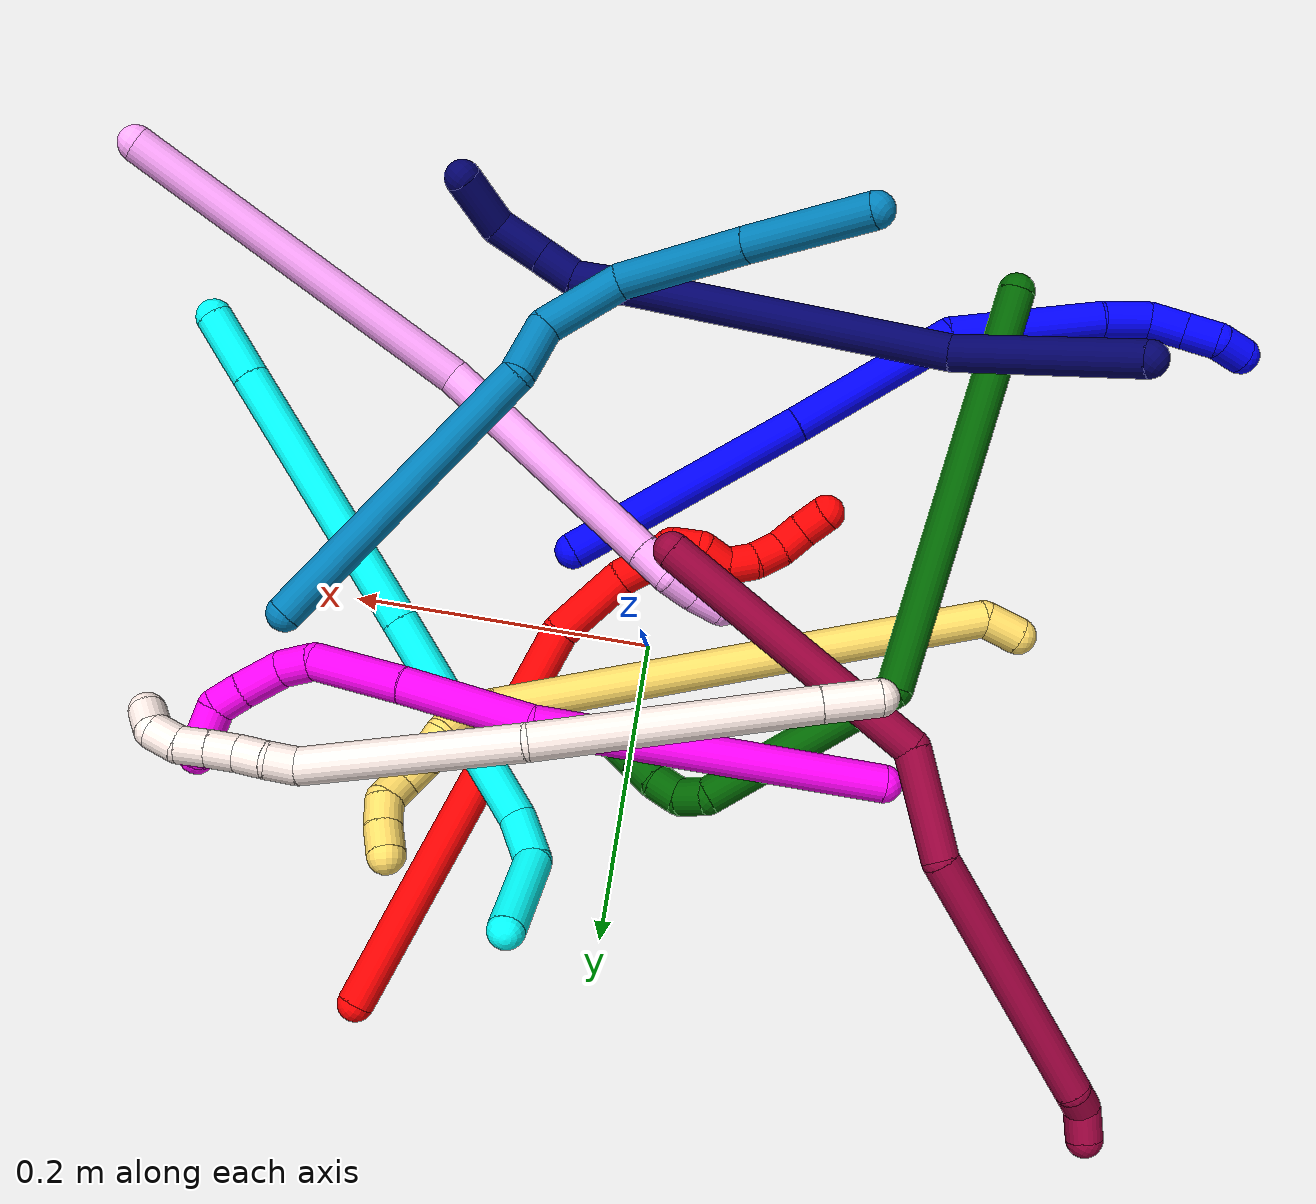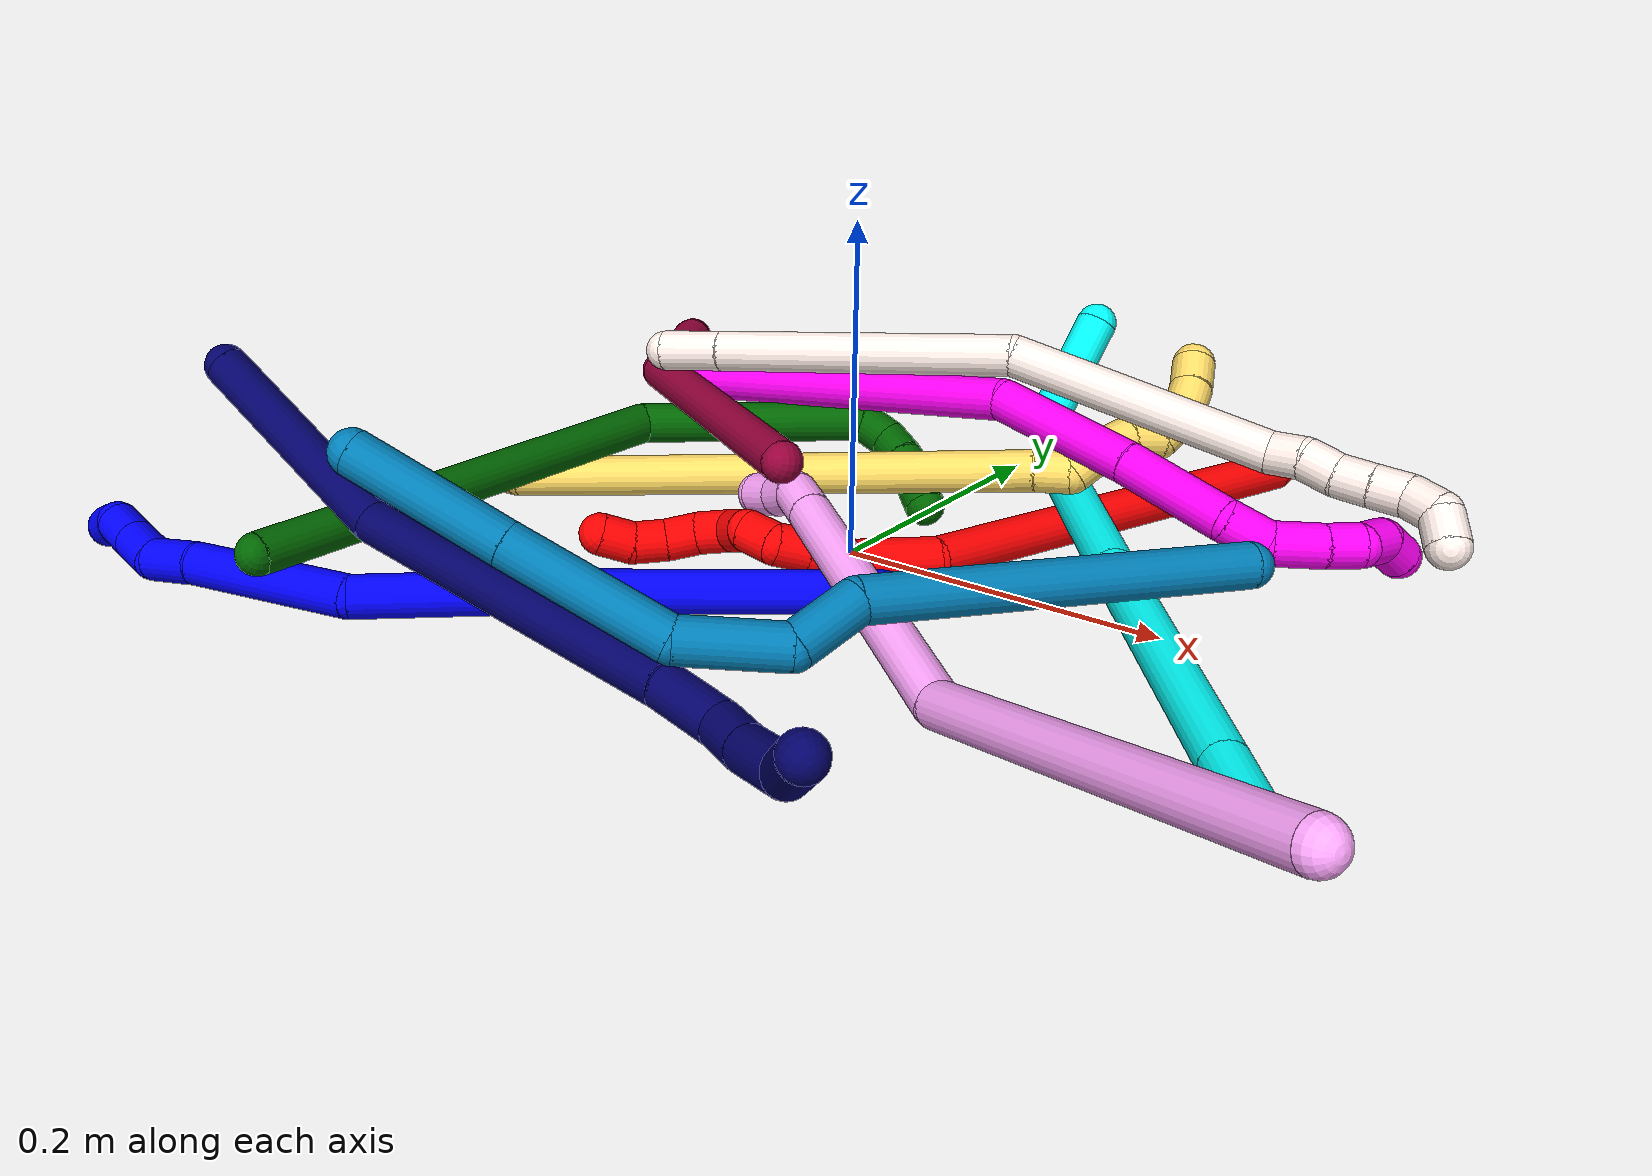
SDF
<sdf version="1.7">
 <world name="default">
  <plugin name="TubeGeneratorPlugin" filename="libtube_generator_plugin.so"/>
  <model name="photoneo_s_sensor">
   <static>1</static>
   <pose>0 0 2 1.57079 1.57079 3.14159</pose>
   <link name="link">
    <inertial><mass>0.1</mass></inertial>
    <sensor name="sensor" type="depth">
     <update_rate>30</update_rate>
     <camera>
      <horizontal_fov>1.22</horizontal_fov>
      <image><width>1920</width><height>1200</height><format>B8G8R8</format></image>
      <clip><near>0.1</near><far>4</far></clip>
      <depth_camera><output>points</output></depth_camera>
     </camera>
     <plugin name="camera_plugin" filename="libgazebo_ros_depth_camera.so">
      <baseline>0.2</baseline>
      <alwaysOn>1</alwaysOn>
      <updateRate>0.0</updateRate>
      <cameraName>camera_ir</cameraName>
      <imageTopicName>/camera/color/image_raw</imageTopicName>
      <cameraInfoTopicName>/camera/color/camera_info</cameraInfoTopicName>
      <depthImageTopicName>/camera/depth/image_raw</depthImageTopicName>
      <depthImageCameraInfoTopicName>/camera/depth/camera_info</depthImageCameraInfoTopicName>
      <pointCloudTopicName>/camera/depth/points</pointCloudTopicName>
      <frameName>fr_optical</frameName>
      <pointCloudCutoff>0.1</pointCloudCutoff>
      <pointCloudCutoffMax>2.0</pointCloudCutoffMax>
      <distortionK1>0</distortionK1>
      <distortionK2>0</distortionK2>
      <distortionK3>0</distortionK3>
      <distortionT1>0</distortionT1>
      <distortionT2>0</distortionT2>
      <CxPrime>0</CxPrime>
      <Cx>0</Cx>
      <Cy>0</Cy>
      <focalLength>0</focalLength>
      <hackBaseline>0</hackBaseline>
     </plugin>
    </sensor>
   </link>
  </model>
  <gravity>0 0 -9.8</gravity>
  <magnetic_field>6e-06 2.3e-05 -4.2e-05</magnetic_field>
  <atmosphere type="adiabatic"/>
  <physics name="default_physics" default="0" type="ode">
   <max_step_size>0.003</max_step_size>
   <real_time_factor>1</real_time_factor>
   <real_time_update_rate>1000</real_time_update_rate>
   <max_contacts>10000</max_contacts>
   <ode>
    <solver>
     <type>quick</type>
     <iters>100</iters>
     <sor>1.3</sor>
     <use_dynamic_moi_rescaling>0</use_dynamic_moi_rescaling>
    </solver>
    <constraints>
     <contact_max_correcting_vel>0</contact_max_correcting_vel>
     <contact_surface_layer>0.001</contact_surface_layer>
     <cfm>0</cfm>
     <erp>0.2</erp>
    </constraints>
   </ode>
  </physics>
  <scene><ambient>0.4 0.4 0.4 1</ambient><background>0.7 0.7 0.7 1</background><shadows>0</shadows></scene>
  <audio><device>default</device></audio>
  <spherical_coordinates>
   <surface_model>EARTH_WGS84</surface_model>
   <latitude_deg>0</latitude_deg>
   <longitude_deg>0</longitude_deg>
   <elevation>0</elevation>
   <heading_deg>0</heading_deg>
  </spherical_coordinates>
  <model name="bin">
   <static>1</static>
   <link name="bottom">
    <collision name="collision-bottom">
     <pose>0 0 -0.01 0 -0 0</pose>
     <geometry><box><size>0.8 0.6 0.02</size></box></geometry>
     <surface>
      <friction><ode><mu>100</mu><mu2>100</mu2></ode></friction>
      <contact><collide_bitmask>65535</collide_bitmask></contact>
     </surface>
    </collision>
   </link>
   <link name="west_wall">
    <collision name="collision-west_wall">
     <pose>-0.41 0 0.1 0 -0 0</pose>
     <geometry><box><size>0.02 0.6 0.2</size></box></geometry>
     <surface>
      <friction><ode><mu>100</mu><mu2>100</mu2></ode></friction>
      <contact><collide_bitmask>65535</collide_bitmask></contact>
     </surface>
    </collision>
   </link>
   <link name="east_wall">
    <collision name="collision-east_wall">
     <pose>0.41 0 0.1 0 -0 0</pose>
     <geometry><box><size>0.02 0.6 0.2</size></box></geometry>
     <surface>
      <friction><ode><mu>100</mu><mu2>100</mu2></ode></friction>
      <contact><collide_bitmask>65535</collide_bitmask></contact>
     </surface>
    </collision>
   </link>
   <link name="south_wall">
    <collision name="collision-south_wall">
     <pose>0 -0.31 0.1 0 -0 0</pose>
     <geometry><box><size>0.8 0.02 0.2</size></box></geometry>
     <surface>
      <friction><ode><mu>100</mu><mu2>100</mu2></ode></friction>
      <contact><collide_bitmask>65535</collide_bitmask></contact>
     </surface>
    </collision>
   </link>
   <link name="north_wall">
    <collision name="collision-north_wall">
     <pose>0 0.31 0.1 0 -0 0</pose>
     <geometry><box><size>0.8 0.02 0.2</size></box></geometry>
     <surface>
      <friction><ode><mu>100</mu><mu2>100</mu2></ode></friction>
      <contact><collide_bitmask>65535</collide_bitmask></contact>
     </surface>
    </collision>
   </link>
  </model>
  <model name="1">
   <static>0</static>
   <link name="1">
    <collision name="collision-cylinder-e_1_1_4">
     <pose>-0.046609 -0.000448 0.073208 0.006125 -0.566937 -0.001784</pose>
     <geometry><cylinder><radius>0.0125</radius><length>0.173574</length></cylinder></geometry>
     <surface>
      <friction><ode><mu>1.16</mu><mu2>1.16</mu2><slip1>0</slip1><slip2>0</slip2></ode></friction>
      <contact><ode><kp>1e+06</kp><kd>1</kd><max_vel>0</max_vel><min_depth>0.001</min_depth></ode></contact>
     </surface>
    </collision>
    <visual name="visual-cylinder-e_1_1_4">
     <pose>-0.046609 -0.000448 0.073208 0.006125 -0.566937 -0.001784</pose>
     <geometry><cylinder><radius>0.0125</radius><length>0.173574</length></cylinder></geometry>
     <material><ambient>0 0 1 1</ambient></material>
    </visual>
    <collision name="collision-cylinder-e_2_4_5">
     <pose>-0.125567 0.000679 0.197621 -0.030757 -0.563217 0.008899</pose>
     <geometry><cylinder><radius>0.0125</radius><length>0.121177</length></cylinder></geometry>
     <surface>
      <friction><ode><mu>1.16</mu><mu2>1.16</mu2><slip1>0</slip1><slip2>0</slip2></ode></friction>
      <contact><ode><kp>1e+06</kp><kd>1</kd><max_vel>0</max_vel><min_depth>0.001</min_depth></ode></contact>
     </surface>
    </collision>
    <visual name="visual-cylinder-e_2_4_5">
     <pose>-0.125567 0.000679 0.197621 -0.030757 -0.563217 0.008899</pose>
     <geometry><cylinder><radius>0.0125</radius><length>0.121177</length></cylinder></geometry>
     <material><ambient>0 0 1 1</ambient></material>
    </visual>
    <collision name="collision-cylinder-e_3_5_6">
     <pose>-0.172079 -0.014183 0.295765 0.336834 -0.277445 -0.047469</pose>
     <geometry><cylinder><radius>0.0125</radius><length>0.103421</length></cylinder></geometry>
     <surface>
      <friction><ode><mu>1.16</mu><mu2>1.16</mu2><slip1>0</slip1><slip2>0</slip2></ode></friction>
      <contact><ode><kp>1e+06</kp><kd>1</kd><max_vel>0</max_vel><min_depth>0.001</min_depth></ode></contact>
     </surface>
    </collision>
    <visual name="visual-cylinder-e_3_5_6">
     <pose>-0.172079 -0.014183 0.295765 0.336834 -0.277445 -0.047469</pose>
     <geometry><cylinder><radius>0.0125</radius><length>0.103421</length></cylinder></geometry>
     <material><ambient>0 0 1 1</ambient></material>
    </visual>
    <collision name="collision-cylinder-e_4_6_7">
     <pose>-0.188231 -0.035077 0.358179 0.280424 -0.122898 -0.017367</pose>
     <geometry><cylinder><radius>0.0125</radius><length>0.032454</length></cylinder></geometry>
     <surface>
      <friction><ode><mu>1.16</mu><mu2>1.16</mu2><slip1>0</slip1><slip2>0</slip2></ode></friction>
      <contact><ode><kp>1e+06</kp><kd>1</kd><max_vel>0</max_vel><min_depth>0.001</min_depth></ode></contact>
     </surface>
    </collision>
    <visual name="visual-cylinder-e_4_6_7">
     <pose>-0.188231 -0.035077 0.358179 0.280424 -0.122898 -0.017367</pose>
     <geometry><cylinder><radius>0.0125</radius><length>0.032454</length></cylinder></geometry>
     <material><ambient>0 0 1 1</ambient></material>
    </visual>
    <collision name="collision-cylinder-e_5_7_8">
     <pose>-0.19057 -0.048029 0.383093 0.732843 -0.027501 -0.010554</pose>
     <geometry><cylinder><radius>0.0125</radius><length>0.025407</length></cylinder></geometry>
     <surface>
      <friction><ode><mu>1.16</mu><mu2>1.16</mu2><slip1>0</slip1><slip2>0</slip2></ode></friction>
      <contact><ode><kp>1e+06</kp><kd>1</kd><max_vel>0</max_vel><min_depth>0.001</min_depth></ode></contact>
     </surface>
    </collision>
    <visual name="visual-cylinder-e_5_7_8">
     <pose>-0.19057 -0.048029 0.383093 0.732843 -0.027501 -0.010554</pose>
     <geometry><cylinder><radius>0.0125</radius><length>0.025407</length></cylinder></geometry>
     <material><ambient>0 0 1 1</ambient></material>
    </visual>
    <collision name="collision-cylinder-e_6_8_9">
     <pose>-0.191324 -0.064373 0.400925 0.751887 -0.035251 -0.013915</pose>
     <geometry><cylinder><radius>0.0125</radius><length>0.022998</length></cylinder></geometry>
     <surface>
      <friction><ode><mu>1.16</mu><mu2>1.16</mu2><slip1>0</slip1><slip2>0</slip2></ode></friction>
      <contact><ode><kp>1e+06</kp><kd>1</kd><max_vel>0</max_vel><min_depth>0.001</min_depth></ode></contact>
     </surface>
    </collision>
    <visual name="visual-cylinder-e_6_8_9">
     <pose>-0.191324 -0.064373 0.400925 0.751887 -0.035251 -0.013915</pose>
     <geometry><cylinder><radius>0.0125</radius><length>0.022998</length></cylinder></geometry>
     <material><ambient>0 0 1 1</ambient></material>
    </visual>
    <collision name="collision-cylinder-e_7_9_2">
     <pose>-0.18761 -0.075183 0.418495 0.312121 0.403773 0.064385</pose>
     <geometry><cylinder><radius>0.0125</radius><length>0.02097</length></cylinder></geometry>
     <surface>
      <friction><ode><mu>1.16</mu><mu2>1.16</mu2><slip1>0</slip1><slip2>0</slip2></ode></friction>
      <contact><ode><kp>1e+06</kp><kd>1</kd><max_vel>0</max_vel><min_depth>0.001</min_depth></ode></contact>
     </surface>
    </collision>
    <visual name="visual-cylinder-e_7_9_2">
     <pose>-0.18761 -0.075183 0.418495 0.312121 0.403773 0.064385</pose>
     <geometry><cylinder><radius>0.0125</radius><length>0.02097</length></cylinder></geometry>
     <material><ambient>0 0 1 1</ambient></material>
    </visual>
    <collision name="collision-sphere-2">
     <pose>-0.183491 -0.078144 0.427671 0 -0 0</pose>
     <geometry><sphere><radius>0.0125</radius></sphere></geometry>
     <surface>
      <friction><ode><mu>1.16</mu><mu2>1.16</mu2><slip1>0</slip1><slip2>0</slip2></ode></friction>
      <contact><ode><kp>1e+06</kp><kd>1</kd><max_vel>0</max_vel><min_depth>0.001</min_depth></ode></contact>
     </surface>
    </collision>
    <visual name="visual-sphere-2">
     <pose>-0.183491 -0.078144 0.427671 0 -0 0</pose>
     <geometry><sphere><radius>0.0125</radius></sphere></geometry>
     <material><ambient>0 0 1 1</ambient></material>
    </visual>
    <collision name="collision-sphere-9">
     <pose>-0.19173 -0.072222 0.409319 0 -0 0</pose>
     <geometry><sphere><radius>0.0125</radius></sphere></geometry>
     <surface>
      <friction><ode><mu>1.16</mu><mu2>1.16</mu2><slip1>0</slip1><slip2>0</slip2></ode></friction>
      <contact><ode><kp>1e+06</kp><kd>1</kd><max_vel>0</max_vel><min_depth>0.001</min_depth></ode></contact>
     </surface>
    </collision>
    <visual name="visual-sphere-9">
     <pose>-0.19173 -0.072222 0.409319 0 -0 0</pose>
     <geometry><sphere><radius>0.0125</radius></sphere></geometry>
     <material><ambient>0 0 1 1</ambient></material>
    </visual>
    <collision name="collision-sphere-4">
     <pose>-0.093218 -0.000897 0.146415 0 -0 0</pose>
     <geometry><sphere><radius>0.0125</radius></sphere></geometry>
     <surface>
      <friction><ode><mu>1.16</mu><mu2>1.16</mu2><slip1>0</slip1><slip2>0</slip2></ode></friction>
      <contact><ode><kp>1e+06</kp><kd>1</kd><max_vel>0</max_vel><min_depth>0.001</min_depth></ode></contact>
     </surface>
    </collision>
    <visual name="visual-sphere-4">
     <pose>-0.093218 -0.000897 0.146415 0 -0 0</pose>
     <geometry><sphere><radius>0.0125</radius></sphere></geometry>
     <material><ambient>0 0 1 1</ambient></material>
    </visual>
    <collision name="collision-sphere-1">
     <geometry><sphere><radius>0.0125</radius></sphere></geometry>
     <surface>
      <friction><ode><mu>1.16</mu><mu2>1.16</mu2><slip1>0</slip1><slip2>0</slip2></ode></friction>
      <contact><ode><kp>1e+06</kp><kd>1</kd><max_vel>0</max_vel><min_depth>0.001</min_depth></ode></contact>
     </surface>
    </collision>
    <visual name="visual-sphere-1">
     <geometry><sphere><radius>0.0125</radius></sphere></geometry>
     <material><ambient>0 0 1 1</ambient></material>
    </visual>
    <collision name="collision-sphere-8">
     <pose>-0.190919 -0.056524 0.392532 0 -0 0</pose>
     <geometry><sphere><radius>0.0125</radius></sphere></geometry>
     <surface>
      <friction><ode><mu>1.16</mu><mu2>1.16</mu2><slip1>0</slip1><slip2>0</slip2></ode></friction>
      <contact><ode><kp>1e+06</kp><kd>1</kd><max_vel>0</max_vel><min_depth>0.001</min_depth></ode></contact>
     </surface>
    </collision>
    <visual name="visual-sphere-8">
     <pose>-0.190919 -0.056524 0.392532 0 -0 0</pose>
     <geometry><sphere><radius>0.0125</radius></sphere></geometry>
     <material><ambient>0 0 1 1</ambient></material>
    </visual>
    <collision name="collision-sphere-5">
     <pose>-0.157915 0.002254 0.248827 0 -0 0</pose>
     <geometry><sphere><radius>0.0125</radius></sphere></geometry>
     <surface>
      <friction><ode><mu>1.16</mu><mu2>1.16</mu2><slip1>0</slip1><slip2>0</slip2></ode></friction>
      <contact><ode><kp>1e+06</kp><kd>1</kd><max_vel>0</max_vel><min_depth>0.001</min_depth></ode></contact>
     </surface>
    </collision>
    <visual name="visual-sphere-5">
     <pose>-0.157915 0.002254 0.248827 0 -0 0</pose>
     <geometry><sphere><radius>0.0125</radius></sphere></geometry>
     <material><ambient>0 0 1 1</ambient></material>
    </visual>
    <collision name="collision-sphere-6">
     <pose>-0.186242 -0.030619 0.342703 0 -0 0</pose>
     <geometry><sphere><radius>0.0125</radius></sphere></geometry>
     <surface>
      <friction><ode><mu>1.16</mu><mu2>1.16</mu2><slip1>0</slip1><slip2>0</slip2></ode></friction>
      <contact><ode><kp>1e+06</kp><kd>1</kd><max_vel>0</max_vel><min_depth>0.001</min_depth></ode></contact>
     </surface>
    </collision>
    <visual name="visual-sphere-6">
     <pose>-0.186242 -0.030619 0.342703 0 -0 0</pose>
     <geometry><sphere><radius>0.0125</radius></sphere></geometry>
     <material><ambient>0 0 1 1</ambient></material>
    </visual>
    <collision name="collision-sphere-7">
     <pose>-0.190221 -0.039534 0.373655 0 -0 0</pose>
     <geometry><sphere><radius>0.0125</radius></sphere></geometry>
     <surface>
      <friction><ode><mu>1.16</mu><mu2>1.16</mu2><slip1>0</slip1><slip2>0</slip2></ode></friction>
      <contact><ode><kp>1e+06</kp><kd>1</kd><max_vel>0</max_vel><min_depth>0.001</min_depth></ode></contact>
     </surface>
    </collision>
    <visual name="visual-sphere-7">
     <pose>-0.190221 -0.039534 0.373655 0 -0 0</pose>
     <geometry><sphere><radius>0.0125</radius></sphere></geometry>
     <material><ambient>0 0 1 1</ambient></material>
    </visual>
    <inertial>
     <pose>-0.120774 -0.013756 0.213192 0 -0 0</pose>
     <mass>0.5</mass>
     <inertia>
      <ixx>0.000587</ixx>
      <ixy>0</ixy>
      <ixz>0</ixz>
      <iyy>0.000685</iyy>
      <iyz>0</iyz>
      <izz>0.000413</izz>
     </inertia>
    </inertial>
   </link>
   <pose>0.060442 -0.055634 0.009029 -2.09292 0.674438 1.49955</pose>
  </model>
  <model name="2">
   <static>0</static>
   <link name="2">
    <collision name="collision-cylinder-e_1_1_4">
     <pose>-0.033796 -0.137193 -0.001831 1.58414 -0.241508 -0.244721</pose>
     <geometry><cylinder><radius>0.0125</radius><length>0.282613</length></cylinder></geometry>
     <surface>
      <friction><ode><mu>1.16</mu><mu2>1.16</mu2><slip1>0</slip1><slip2>0</slip2></ode></friction>
      <contact><ode><kp>1e+06</kp><kd>1</kd><max_vel>0</max_vel><min_depth>0.001</min_depth></ode></contact>
     </surface>
    </collision>
    <visual name="visual-cylinder-e_1_1_4">
     <pose>-0.033796 -0.137193 -0.001831 1.58414 -0.241508 -0.244721</pose>
     <geometry><cylinder><radius>0.0125</radius><length>0.282613</length></cylinder></geometry>
     <material><ambient>1 0 0 1</ambient></material>
    </visual>
    <collision name="collision-cylinder-e_2_4_5">
     <pose>-0.079992 -0.297947 -0.011154 1.87865 -0.464911 -0.626091</pose>
     <geometry><cylinder><radius>0.0125</radius><length>0.055316</length></cylinder></geometry>
     <surface>
      <friction><ode><mu>1.16</mu><mu2>1.16</mu2><slip1>0</slip1><slip2>0</slip2></ode></friction>
      <contact><ode><kp>1e+06</kp><kd>1</kd><max_vel>0</max_vel><min_depth>0.001</min_depth></ode></contact>
     </surface>
    </collision>
    <visual name="visual-cylinder-e_2_4_5">
     <pose>-0.079992 -0.297947 -0.011154 1.87865 -0.464911 -0.626091</pose>
     <geometry><cylinder><radius>0.0125</radius><length>0.055316</length></cylinder></geometry>
     <material><ambient>1 0 0 1</ambient></material>
    </visual>
    <collision name="collision-cylinder-e_3_5_6">
     <pose>-0.099783 -0.32802 -0.022099 2.05838 -0.786652 -1.20759</pose>
     <geometry><cylinder><radius>0.0125</radius><length>0.020878</length></cylinder></geometry>
     <surface>
      <friction><ode><mu>1.16</mu><mu2>1.16</mu2><slip1>0</slip1><slip2>0</slip2></ode></friction>
      <contact><ode><kp>1e+06</kp><kd>1</kd><max_vel>0</max_vel><min_depth>0.001</min_depth></ode></contact>
     </surface>
    </collision>
    <visual name="visual-cylinder-e_3_5_6">
     <pose>-0.099783 -0.32802 -0.022099 2.05838 -0.786652 -1.20759</pose>
     <geometry><cylinder><radius>0.0125</radius><length>0.020878</length></cylinder></geometry>
     <material><ambient>1 0 0 1</ambient></material>
    </visual>
    <collision name="collision-cylinder-e_4_6_7">
     <pose>-0.113868 -0.342223 -0.027759 1.85023 -0.696734 -0.898365</pose>
     <geometry><cylinder><radius>0.0125</radius><length>0.020863</length></cylinder></geometry>
     <surface>
      <friction><ode><mu>1.16</mu><mu2>1.16</mu2><slip1>0</slip1><slip2>0</slip2></ode></friction>
      <contact><ode><kp>1e+06</kp><kd>1</kd><max_vel>0</max_vel><min_depth>0.001</min_depth></ode></contact>
     </surface>
    </collision>
    <visual name="visual-cylinder-e_4_6_7">
     <pose>-0.113868 -0.342223 -0.027759 1.85023 -0.696734 -0.898365</pose>
     <geometry><cylinder><radius>0.0125</radius><length>0.020863</length></cylinder></geometry>
     <material><ambient>1 0 0 1</ambient></material>
    </visual>
    <collision name="collision-cylinder-e_5_7_8">
     <pose>-0.127657 -0.351523 -0.036827 2.9111 -0.788715 -2.59898</pose>
     <geometry><cylinder><radius>0.0125</radius><length>0.020001</length></cylinder></geometry>
     <surface>
      <friction><ode><mu>1.16</mu><mu2>1.16</mu2><slip1>0</slip1><slip2>0</slip2></ode></friction>
      <contact><ode><kp>1e+06</kp><kd>1</kd><max_vel>0</max_vel><min_depth>0.001</min_depth></ode></contact>
     </surface>
    </collision>
    <visual name="visual-cylinder-e_5_7_8">
     <pose>-0.127657 -0.351523 -0.036827 2.9111 -0.788715 -2.59898</pose>
     <geometry><cylinder><radius>0.0125</radius><length>0.020001</length></cylinder></geometry>
     <material><ambient>1 0 0 1</ambient></material>
    </visual>
    <collision name="collision-cylinder-e_6_8_9">
     <pose>-0.136851 -0.351537 -0.053388 -2.97846 -0.210443 1.8242</pose>
     <geometry><cylinder><radius>0.0125</radius><length>0.020102</length></cylinder></geometry>
     <surface>
      <friction><ode><mu>1.16</mu><mu2>1.16</mu2><slip1>0</slip1><slip2>0</slip2></ode></friction>
      <contact><ode><kp>1e+06</kp><kd>1</kd><max_vel>0</max_vel><min_depth>0.001</min_depth></ode></contact>
     </surface>
    </collision>
    <visual name="visual-cylinder-e_6_8_9">
     <pose>-0.136851 -0.351537 -0.053388 -2.97846 -0.210443 1.8242</pose>
     <geometry><cylinder><radius>0.0125</radius><length>0.020102</length></cylinder></geometry>
     <material><ambient>1 0 0 1</ambient></material>
    </visual>
    <collision name="collision-cylinder-e_7_9_10">
     <pose>-0.14292 -0.355347 -0.070584 2.51683 -0.405623 -1.13399</pose>
     <geometry><cylinder><radius>0.0125</radius><length>0.020118</length></cylinder></geometry>
     <surface>
      <friction><ode><mu>1.16</mu><mu2>1.16</mu2><slip1>0</slip1><slip2>0</slip2></ode></friction>
      <contact><ode><kp>1e+06</kp><kd>1</kd><max_vel>0</max_vel><min_depth>0.001</min_depth></ode></contact>
     </surface>
    </collision>
    <visual name="visual-cylinder-e_7_9_10">
     <pose>-0.14292 -0.355347 -0.070584 2.51683 -0.405623 -1.13399</pose>
     <geometry><cylinder><radius>0.0125</radius><length>0.020118</length></cylinder></geometry>
     <material><ambient>1 0 0 1</ambient></material>
    </visual>
    <collision name="collision-cylinder-e_8_10_11">
     <pose>-0.149825 -0.368186 -0.084093 2.25096 -0.297907 -0.609247</pose>
     <geometry><cylinder><radius>0.0125</radius><length>0.020002</length></cylinder></geometry>
     <surface>
      <friction><ode><mu>1.16</mu><mu2>1.16</mu2><slip1>0</slip1><slip2>0</slip2></ode></friction>
      <contact><ode><kp>1e+06</kp><kd>1</kd><max_vel>0</max_vel><min_depth>0.001</min_depth></ode></contact>
     </surface>
    </collision>
    <visual name="visual-cylinder-e_8_10_11">
     <pose>-0.149825 -0.368186 -0.084093 2.25096 -0.297907 -0.609247</pose>
     <geometry><cylinder><radius>0.0125</radius><length>0.020002</length></cylinder></geometry>
     <material><ambient>1 0 0 1</ambient></material>
    </visual>
    <collision name="collision-cylinder-e_9_11_12">
     <pose>-0.156824 -0.384148 -0.093435 1.94295 -0.417764 -0.601749</pose>
     <geometry><cylinder><radius>0.0125</radius><length>0.020034</length></cylinder></geometry>
     <surface>
      <friction><ode><mu>1.16</mu><mu2>1.16</mu2><slip1>0</slip1><slip2>0</slip2></ode></friction>
      <contact><ode><kp>1e+06</kp><kd>1</kd><max_vel>0</max_vel><min_depth>0.001</min_depth></ode></contact>
     </surface>
    </collision>
    <visual name="visual-cylinder-e_9_11_12">
     <pose>-0.156824 -0.384148 -0.093435 1.94295 -0.417764 -0.601749</pose>
     <geometry><cylinder><radius>0.0125</radius><length>0.020034</length></cylinder></geometry>
     <material><ambient>1 0 0 1</ambient></material>
    </visual>
    <collision name="collision-cylinder-e_10_12_2">
     <pose>-0.167802 -0.39967 -0.098774 1.8506 -0.759863 -0.975087</pose>
     <geometry><cylinder><radius>0.0125</radius><length>0.020072</length></cylinder></geometry>
     <surface>
      <friction><ode><mu>1.16</mu><mu2>1.16</mu2><slip1>0</slip1><slip2>0</slip2></ode></friction>
      <contact><ode><kp>1e+06</kp><kd>1</kd><max_vel>0</max_vel><min_depth>0.001</min_depth></ode></contact>
     </surface>
    </collision>
    <visual name="visual-cylinder-e_10_12_2">
     <pose>-0.167802 -0.39967 -0.098774 1.8506 -0.759863 -0.975087</pose>
     <geometry><cylinder><radius>0.0125</radius><length>0.020072</length></cylinder></geometry>
     <material><ambient>1 0 0 1</ambient></material>
    </visual>
    <collision name="collision-sphere-2">
     <pose>-0.174715 -0.406662 -0.100783 0 -0 0</pose>
     <geometry><sphere><radius>0.0125</radius></sphere></geometry>
     <surface>
      <friction><ode><mu>1.16</mu><mu2>1.16</mu2><slip1>0</slip1><slip2>0</slip2></ode></friction>
      <contact><ode><kp>1e+06</kp><kd>1</kd><max_vel>0</max_vel><min_depth>0.001</min_depth></ode></contact>
     </surface>
    </collision>
    <visual name="visual-sphere-2">
     <pose>-0.174715 -0.406662 -0.100783 0 -0 0</pose>
     <geometry><sphere><radius>0.0125</radius></sphere></geometry>
     <material><ambient>1 0 0 1</ambient></material>
    </visual>
    <collision name="collision-sphere-12">
     <pose>-0.160889 -0.392677 -0.096764 0 -0 0</pose>
     <geometry><sphere><radius>0.0125</radius></sphere></geometry>
     <surface>
      <friction><ode><mu>1.16</mu><mu2>1.16</mu2><slip1>0</slip1><slip2>0</slip2></ode></friction>
      <contact><ode><kp>1e+06</kp><kd>1</kd><max_vel>0</max_vel><min_depth>0.001</min_depth></ode></contact>
     </surface>
    </collision>
    <visual name="visual-sphere-12">
     <pose>-0.160889 -0.392677 -0.096764 0 -0 0</pose>
     <geometry><sphere><radius>0.0125</radius></sphere></geometry>
     <material><ambient>1 0 0 1</ambient></material>
    </visual>
    <collision name="collision-sphere-11">
     <pose>-0.15276 -0.375619 -0.090106 0 -0 0</pose>
     <geometry><sphere><radius>0.0125</radius></sphere></geometry>
     <surface>
      <friction><ode><mu>1.16</mu><mu2>1.16</mu2><slip1>0</slip1><slip2>0</slip2></ode></friction>
      <contact><ode><kp>1e+06</kp><kd>1</kd><max_vel>0</max_vel><min_depth>0.001</min_depth></ode></contact>
     </surface>
    </collision>
    <visual name="visual-sphere-11">
     <pose>-0.15276 -0.375619 -0.090106 0 -0 0</pose>
     <geometry><sphere><radius>0.0125</radius></sphere></geometry>
     <material><ambient>1 0 0 1</ambient></material>
    </visual>
    <collision name="collision-sphere-10">
     <pose>-0.146889 -0.360753 -0.07808 0 -0 0</pose>
     <geometry><sphere><radius>0.0125</radius></sphere></geometry>
     <surface>
      <friction><ode><mu>1.16</mu><mu2>1.16</mu2><slip1>0</slip1><slip2>0</slip2></ode></friction>
      <contact><ode><kp>1e+06</kp><kd>1</kd><max_vel>0</max_vel><min_depth>0.001</min_depth></ode></contact>
     </surface>
    </collision>
    <visual name="visual-sphere-10">
     <pose>-0.146889 -0.360753 -0.07808 0 -0 0</pose>
     <geometry><sphere><radius>0.0125</radius></sphere></geometry>
     <material><ambient>1 0 0 1</ambient></material>
    </visual>
    <collision name="collision-sphere-9">
     <pose>-0.138951 -0.349941 -0.063087 0 -0 0</pose>
     <geometry><sphere><radius>0.0125</radius></sphere></geometry>
     <surface>
      <friction><ode><mu>1.16</mu><mu2>1.16</mu2><slip1>0</slip1><slip2>0</slip2></ode></friction>
      <contact><ode><kp>1e+06</kp><kd>1</kd><max_vel>0</max_vel><min_depth>0.001</min_depth></ode></contact>
     </surface>
    </collision>
    <visual name="visual-sphere-9">
     <pose>-0.138951 -0.349941 -0.063087 0 -0 0</pose>
     <geometry><sphere><radius>0.0125</radius></sphere></geometry>
     <material><ambient>1 0 0 1</ambient></material>
    </visual>
    <collision name="collision-sphere-4">
     <pose>-0.067592 -0.274387 -0.003662 0 -0 0</pose>
     <geometry><sphere><radius>0.0125</radius></sphere></geometry>
     <surface>
      <friction><ode><mu>1.16</mu><mu2>1.16</mu2><slip1>0</slip1><slip2>0</slip2></ode></friction>
      <contact><ode><kp>1e+06</kp><kd>1</kd><max_vel>0</max_vel><min_depth>0.001</min_depth></ode></contact>
     </surface>
    </collision>
    <visual name="visual-sphere-4">
     <pose>-0.067592 -0.274387 -0.003662 0 -0 0</pose>
     <geometry><sphere><radius>0.0125</radius></sphere></geometry>
     <material><ambient>1 0 0 1</ambient></material>
    </visual>
    <collision name="collision-sphere-1">
     <geometry><sphere><radius>0.0125</radius></sphere></geometry>
     <surface>
      <friction><ode><mu>1.16</mu><mu2>1.16</mu2><slip1>0</slip1><slip2>0</slip2></ode></friction>
      <contact><ode><kp>1e+06</kp><kd>1</kd><max_vel>0</max_vel><min_depth>0.001</min_depth></ode></contact>
     </surface>
    </collision>
    <visual name="visual-sphere-1">
     <geometry><sphere><radius>0.0125</radius></sphere></geometry>
     <material><ambient>1 0 0 1</ambient></material>
    </visual>
    <collision name="collision-sphere-8">
     <pose>-0.134752 -0.353134 -0.043689 0 -0 0</pose>
     <geometry><sphere><radius>0.0125</radius></sphere></geometry>
     <surface>
      <friction><ode><mu>1.16</mu><mu2>1.16</mu2><slip1>0</slip1><slip2>0</slip2></ode></friction>
      <contact><ode><kp>1e+06</kp><kd>1</kd><max_vel>0</max_vel><min_depth>0.001</min_depth></ode></contact>
     </surface>
    </collision>
    <visual name="visual-sphere-8">
     <pose>-0.134752 -0.353134 -0.043689 0 -0 0</pose>
     <geometry><sphere><radius>0.0125</radius></sphere></geometry>
     <material><ambient>1 0 0 1</ambient></material>
    </visual>
    <collision name="collision-sphere-5">
     <pose>-0.092392 -0.321507 -0.018645 0 -0 0</pose>
     <geometry><sphere><radius>0.0125</radius></sphere></geometry>
     <surface>
      <friction><ode><mu>1.16</mu><mu2>1.16</mu2><slip1>0</slip1><slip2>0</slip2></ode></friction>
      <contact><ode><kp>1e+06</kp><kd>1</kd><max_vel>0</max_vel><min_depth>0.001</min_depth></ode></contact>
     </surface>
    </collision>
    <visual name="visual-sphere-5">
     <pose>-0.092392 -0.321507 -0.018645 0 -0 0</pose>
     <geometry><sphere><radius>0.0125</radius></sphere></geometry>
     <material><ambient>1 0 0 1</ambient></material>
    </visual>
    <collision name="collision-sphere-6">
     <pose>-0.107174 -0.334533 -0.025552 0 -0 0</pose>
     <geometry><sphere><radius>0.0125</radius></sphere></geometry>
     <surface>
      <friction><ode><mu>1.16</mu><mu2>1.16</mu2><slip1>0</slip1><slip2>0</slip2></ode></friction>
      <contact><ode><kp>1e+06</kp><kd>1</kd><max_vel>0</max_vel><min_depth>0.001</min_depth></ode></contact>
     </surface>
    </collision>
    <visual name="visual-sphere-6">
     <pose>-0.107174 -0.334533 -0.025552 0 -0 0</pose>
     <geometry><sphere><radius>0.0125</radius></sphere></geometry>
     <material><ambient>1 0 0 1</ambient></material>
    </visual>
    <collision name="collision-sphere-7">
     <pose>-0.120562 -0.349913 -0.029966 0 -0 0</pose>
     <geometry><sphere><radius>0.0125</radius></sphere></geometry>
     <surface>
      <friction><ode><mu>1.16</mu><mu2>1.16</mu2><slip1>0</slip1><slip2>0</slip2></ode></friction>
      <contact><ode><kp>1e+06</kp><kd>1</kd><max_vel>0</max_vel><min_depth>0.001</min_depth></ode></contact>
     </surface>
    </collision>
    <visual name="visual-sphere-7">
     <pose>-0.120562 -0.349913 -0.029966 0 -0 0</pose>
     <geometry><sphere><radius>0.0125</radius></sphere></geometry>
     <material><ambient>1 0 0 1</ambient></material>
    </visual>
    <inertial>
     <pose>-0.072243 -0.227143 -0.021883 0 -0 0</pose>
     <mass>0.5</mass>
     <inertia>
      <ixx>0.001325</ixx>
      <ixy>0</ixy>
      <ixz>0</ixz>
      <iyy>-0.000402</iyy>
      <iyz>0</iyz>
      <izz>0.002315</izz>
     </inertia>
    </inertial>
   </link>
   <pose>0.15329 0.266976 0.011496 0.339896 0.952012 0.088383</pose>
  </model>
  <model name="3">
   <static>0</static>
   <link name="3">
    <collision name="collision-cylinder-e_1_1_4">
     <pose>-0.014119 0.017266 0.010557 -1.02203 -0.609152 0.348933</pose>
     <geometry><cylinder><radius>0.0125</radius><length>0.049352</length></cylinder></geometry>
     <surface>
      <friction><ode><mu>1.16</mu><mu2>1.16</mu2><slip1>0</slip1><slip2>0</slip2></ode></friction>
      <contact><ode><kp>1e+06</kp><kd>1</kd><max_vel>0</max_vel><min_depth>0.001</min_depth></ode></contact>
     </surface>
    </collision>
    <visual name="visual-cylinder-e_1_1_4">
     <pose>-0.014119 0.017266 0.010557 -1.02203 -0.609152 0.348933</pose>
     <geometry><cylinder><radius>0.0125</radius><length>0.049352</length></cylinder></geometry>
     <material><ambient>0.003922 1 0.996078 1</ambient></material>
    </visual>
    <collision name="collision-cylinder-e_2_4_5">
     <pose>-0.084763 0.103156 0.062581 -1.02724 -0.614066 0.353977</pose>
     <geometry><cylinder><radius>0.0125</radius><length>0.196202</length></cylinder></geometry>
     <surface>
      <friction><ode><mu>1.16</mu><mu2>1.16</mu2><slip1>0</slip1><slip2>0</slip2></ode></friction>
      <contact><ode><kp>1e+06</kp><kd>1</kd><max_vel>0</max_vel><min_depth>0.001</min_depth></ode></contact>
     </surface>
    </collision>
    <visual name="visual-cylinder-e_2_4_5">
     <pose>-0.084763 0.103156 0.062581 -1.02724 -0.614066 0.353977</pose>
     <geometry><cylinder><radius>0.0125</radius><length>0.196202</length></cylinder></geometry>
     <material><ambient>0.003922 1 0.996078 1</ambient></material>
    </visual>
    <collision name="collision-cylinder-e_3_5_6">
     <pose>-0.184605 0.225233 0.1369 -1.01971 -0.60424 0.345076</pose>
     <geometry><cylinder><radius>0.0125</radius><length>0.152484</length></cylinder></geometry>
     <surface>
      <friction><ode><mu>1.16</mu><mu2>1.16</mu2><slip1>0</slip1><slip2>0</slip2></ode></friction>
      <contact><ode><kp>1e+06</kp><kd>1</kd><max_vel>0</max_vel><min_depth>0.001</min_depth></ode></contact>
     </surface>
    </collision>
    <visual name="visual-cylinder-e_3_5_6">
     <pose>-0.184605 0.225233 0.1369 -1.01971 -0.60424 0.345076</pose>
     <geometry><cylinder><radius>0.0125</radius><length>0.152484</length></cylinder></geometry>
     <material><ambient>0.003922 1 0.996078 1</ambient></material>
    </visual>
    <collision name="collision-cylinder-e_4_6_7">
     <pose>-0.234196 0.286289 0.185246 -0.456218 -0.34875 0.081747</pose>
     <geometry><cylinder><radius>0.0125</radius><length>0.036728</length></cylinder></geometry>
     <surface>
      <friction><ode><mu>1.16</mu><mu2>1.16</mu2><slip1>0</slip1><slip2>0</slip2></ode></friction>
      <contact><ode><kp>1e+06</kp><kd>1</kd><max_vel>0</max_vel><min_depth>0.001</min_depth></ode></contact>
     </surface>
    </collision>
    <visual name="visual-cylinder-e_4_6_7">
     <pose>-0.234196 0.286289 0.185246 -0.456218 -0.34875 0.081747</pose>
     <geometry><cylinder><radius>0.0125</radius><length>0.036728</length></cylinder></geometry>
     <material><ambient>0.003922 1 0.996078 1</ambient></material>
    </visual>
    <collision name="collision-cylinder-e_5_7_2">
     <pose>-0.233897 0.302332 0.231553 -0.267321 0.202948 -0.027381</pose>
     <geometry><cylinder><radius>0.0125</radius><length>0.065234</length></cylinder></geometry>
     <surface>
      <friction><ode><mu>1.16</mu><mu2>1.16</mu2><slip1>0</slip1><slip2>0</slip2></ode></friction>
      <contact><ode><kp>1e+06</kp><kd>1</kd><max_vel>0</max_vel><min_depth>0.001</min_depth></ode></contact>
     </surface>
    </collision>
    <visual name="visual-cylinder-e_5_7_2">
     <pose>-0.233897 0.302332 0.231553 -0.267321 0.202948 -0.027381</pose>
     <geometry><cylinder><radius>0.0125</radius><length>0.065234</length></cylinder></geometry>
     <material><ambient>0.003922 1 0.996078 1</ambient></material>
    </visual>
    <collision name="collision-sphere-2">
     <pose>-0.227323 0.310771 0.262365 0 -0 0</pose>
     <geometry><sphere><radius>0.0125</radius></sphere></geometry>
     <surface>
      <friction><ode><mu>1.16</mu><mu2>1.16</mu2><slip1>0</slip1><slip2>0</slip2></ode></friction>
      <contact><ode><kp>1e+06</kp><kd>1</kd><max_vel>0</max_vel><min_depth>0.001</min_depth></ode></contact>
     </surface>
    </collision>
    <visual name="visual-sphere-2">
     <pose>-0.227323 0.310771 0.262365 0 -0 0</pose>
     <geometry><sphere><radius>0.0125</radius></sphere></geometry>
     <material><ambient>0.003922 1 0.996078 1</ambient></material>
    </visual>
    <collision name="collision-sphere-7">
     <pose>-0.240471 0.293893 0.20074 0 -0 0</pose>
     <geometry><sphere><radius>0.0125</radius></sphere></geometry>
     <surface>
      <friction><ode><mu>1.16</mu><mu2>1.16</mu2><slip1>0</slip1><slip2>0</slip2></ode></friction>
      <contact><ode><kp>1e+06</kp><kd>1</kd><max_vel>0</max_vel><min_depth>0.001</min_depth></ode></contact>
     </surface>
    </collision>
    <visual name="visual-sphere-7">
     <pose>-0.240471 0.293893 0.20074 0 -0 0</pose>
     <geometry><sphere><radius>0.0125</radius></sphere></geometry>
     <material><ambient>0.003922 1 0.996078 1</ambient></material>
    </visual>
    <collision name="collision-sphere-6">
     <pose>-0.22792 0.278686 0.169753 0 -0 0</pose>
     <geometry><sphere><radius>0.0125</radius></sphere></geometry>
     <surface>
      <friction><ode><mu>1.16</mu><mu2>1.16</mu2><slip1>0</slip1><slip2>0</slip2></ode></friction>
      <contact><ode><kp>1e+06</kp><kd>1</kd><max_vel>0</max_vel><min_depth>0.001</min_depth></ode></contact>
     </surface>
    </collision>
    <visual name="visual-sphere-6">
     <pose>-0.22792 0.278686 0.169753 0 -0 0</pose>
     <geometry><sphere><radius>0.0125</radius></sphere></geometry>
     <material><ambient>0.003922 1 0.996078 1</ambient></material>
    </visual>
    <collision name="collision-sphere-5">
     <pose>-0.141289 0.171779 0.104048 0 -0 0</pose>
     <geometry><sphere><radius>0.0125</radius></sphere></geometry>
     <surface>
      <friction><ode><mu>1.16</mu><mu2>1.16</mu2><slip1>0</slip1><slip2>0</slip2></ode></friction>
      <contact><ode><kp>1e+06</kp><kd>1</kd><max_vel>0</max_vel><min_depth>0.001</min_depth></ode></contact>
     </surface>
    </collision>
    <visual name="visual-sphere-5">
     <pose>-0.141289 0.171779 0.104048 0 -0 0</pose>
     <geometry><sphere><radius>0.0125</radius></sphere></geometry>
     <material><ambient>0.003922 1 0.996078 1</ambient></material>
    </visual>
    <collision name="collision-sphere-1">
     <geometry><sphere><radius>0.0125</radius></sphere></geometry>
     <surface>
      <friction><ode><mu>1.16</mu><mu2>1.16</mu2><slip1>0</slip1><slip2>0</slip2></ode></friction>
      <contact><ode><kp>1e+06</kp><kd>1</kd><max_vel>0</max_vel><min_depth>0.001</min_depth></ode></contact>
     </surface>
    </collision>
    <visual name="visual-sphere-1">
     <geometry><sphere><radius>0.0125</radius></sphere></geometry>
     <material><ambient>0.003922 1 0.996078 1</ambient></material>
    </visual>
    <collision name="collision-sphere-4">
     <pose>-0.028238 0.034532 0.021113 0 -0 0</pose>
     <geometry><sphere><radius>0.0125</radius></sphere></geometry>
     <surface>
      <friction><ode><mu>1.16</mu><mu2>1.16</mu2><slip1>0</slip1><slip2>0</slip2></ode></friction>
      <contact><ode><kp>1e+06</kp><kd>1</kd><max_vel>0</max_vel><min_depth>0.001</min_depth></ode></contact>
     </surface>
    </collision>
    <visual name="visual-sphere-4">
     <pose>-0.028238 0.034532 0.021113 0 -0 0</pose>
     <geometry><sphere><radius>0.0125</radius></sphere></geometry>
     <material><ambient>0.003922 1 0.996078 1</ambient></material>
    </visual>
    <inertial>
     <pose>-0.138673 0.171346 0.111167 0 -0 0</pose>
     <mass>0.5</mass>
     <inertia>
      <ixx>0.001011</ixx>
      <ixy>0</ixy>
      <ixz>0</ixz>
      <iyy>0.000945</iyy>
      <iyz>0</iyz>
      <izz>-0.000112</izz>
     </inertia>
    </inertial>
   </link>
   <pose>0.326694 -0.172683 0.011496 -0.421187 -0.060674 0.100629</pose>
  </model>
  <model name="4">
   <static>0</static>
   <link name="4">
    <collision name="collision-cylinder-e_1_1_4">
     <pose>0.007169 0.001727 -0.126411 -3.12793 0.056647 -2.66851</pose>
     <geometry><cylinder><radius>0.0125</radius><length>0.253251</length></cylinder></geometry>
     <surface>
      <friction><ode><mu>1.16</mu><mu2>1.16</mu2><slip1>0</slip1><slip2>0</slip2></ode></friction>
      <contact><ode><kp>1e+06</kp><kd>1</kd><max_vel>0</max_vel><min_depth>0.001</min_depth></ode></contact>
     </surface>
    </collision>
    <visual name="visual-cylinder-e_1_1_4">
     <pose>0.007169 0.001727 -0.126411 -3.12793 0.056647 -2.66851</pose>
     <geometry><cylinder><radius>0.0125</radius><length>0.253251</length></cylinder></geometry>
     <material><ambient>1 0.65098 0.996078 1</ambient></material>
    </visual>
    <collision name="collision-cylinder-e_2_4_5">
     <pose>-0.003632 0.035721 -0.335241 -2.76843 -0.2003 0.978316</pose>
     <geometry><cylinder><radius>0.0125</radius><length>0.180633</length></cylinder></geometry>
     <surface>
      <friction><ode><mu>1.16</mu><mu2>1.16</mu2><slip1>0</slip1><slip2>0</slip2></ode></friction>
      <contact><ode><kp>1e+06</kp><kd>1</kd><max_vel>0</max_vel><min_depth>0.001</min_depth></ode></contact>
     </surface>
    </collision>
    <visual name="visual-cylinder-e_2_4_5">
     <pose>-0.003632 0.035721 -0.335241 -2.76843 -0.2003 0.978316</pose>
     <geometry><cylinder><radius>0.0125</radius><length>0.180633</length></cylinder></geometry>
     <material><ambient>1 0.65098 0.996078 1</ambient></material>
    </visual>
    <collision name="collision-cylinder-e_3_5_6">
     <pose>-0.02389 0.072186 -0.428824 -2.78195 -0.189585 0.963779</pose>
     <geometry><cylinder><radius>0.0125</radius><length>0.024289</length></cylinder></geometry>
     <surface>
      <friction><ode><mu>1.16</mu><mu2>1.16</mu2><slip1>0</slip1><slip2>0</slip2></ode></friction>
      <contact><ode><kp>1e+06</kp><kd>1</kd><max_vel>0</max_vel><min_depth>0.001</min_depth></ode></contact>
     </surface>
    </collision>
    <visual name="visual-cylinder-e_3_5_6">
     <pose>-0.02389 0.072186 -0.428824 -2.78195 -0.189585 0.963779</pose>
     <geometry><cylinder><radius>0.0125</radius><length>0.024289</length></cylinder></geometry>
     <material><ambient>1 0.65098 0.996078 1</ambient></material>
    </visual>
    <collision name="collision-cylinder-e_4_6_7">
     <pose>-0.024593 0.075357 -0.45006 3.04007 0.155354 1.98499</pose>
     <geometry><cylinder><radius>0.0125</radius><length>0.020496</length></cylinder></geometry>
     <surface>
      <friction><ode><mu>1.16</mu><mu2>1.16</mu2><slip1>0</slip1><slip2>0</slip2></ode></friction>
      <contact><ode><kp>1e+06</kp><kd>1</kd><max_vel>0</max_vel><min_depth>0.001</min_depth></ode></contact>
     </surface>
    </collision>
    <visual name="visual-cylinder-e_4_6_7">
     <pose>-0.024593 0.075357 -0.45006 3.04007 0.155354 1.98499</pose>
     <geometry><cylinder><radius>0.0125</radius><length>0.020496</length></cylinder></geometry>
     <material><ambient>1 0.65098 0.996078 1</ambient></material>
    </visual>
    <collision name="collision-cylinder-e_5_7_2">
     <pose>-0.022886 0.072983 -0.470712 3.01487 0.011342 0.178294</pose>
     <geometry><cylinder><radius>0.0125</radius><length>0.021331</length></cylinder></geometry>
     <surface>
      <friction><ode><mu>1.16</mu><mu2>1.16</mu2><slip1>0</slip1><slip2>0</slip2></ode></friction>
      <contact><ode><kp>1e+06</kp><kd>1</kd><max_vel>0</max_vel><min_depth>0.001</min_depth></ode></contact>
     </surface>
    </collision>
    <visual name="visual-cylinder-e_5_7_2">
     <pose>-0.022886 0.072983 -0.470712 3.01487 0.011342 0.178294</pose>
     <geometry><cylinder><radius>0.0125</radius><length>0.021331</length></cylinder></geometry>
     <material><ambient>1 0.65098 0.996078 1</ambient></material>
    </visual>
    <collision name="collision-sphere-2">
     <pose>-0.022765 0.071635 -0.481291 0 -0 0</pose>
     <geometry><sphere><radius>0.0125</radius></sphere></geometry>
     <surface>
      <friction><ode><mu>1.16</mu><mu2>1.16</mu2><slip1>0</slip1><slip2>0</slip2></ode></friction>
      <contact><ode><kp>1e+06</kp><kd>1</kd><max_vel>0</max_vel><min_depth>0.001</min_depth></ode></contact>
     </surface>
    </collision>
    <visual name="visual-sphere-2">
     <pose>-0.022765 0.071635 -0.481291 0 -0 0</pose>
     <geometry><sphere><radius>0.0125</radius></sphere></geometry>
     <material><ambient>1 0.65098 0.996078 1</ambient></material>
    </visual>
    <collision name="collision-sphere-7">
     <pose>-0.023007 0.074331 -0.460132 0 -0 0</pose>
     <geometry><sphere><radius>0.0125</radius></sphere></geometry>
     <surface>
      <friction><ode><mu>1.16</mu><mu2>1.16</mu2><slip1>0</slip1><slip2>0</slip2></ode></friction>
      <contact><ode><kp>1e+06</kp><kd>1</kd><max_vel>0</max_vel><min_depth>0.001</min_depth></ode></contact>
     </surface>
    </collision>
    <visual name="visual-sphere-7">
     <pose>-0.023007 0.074331 -0.460132 0 -0 0</pose>
     <geometry><sphere><radius>0.0125</radius></sphere></geometry>
     <material><ambient>1 0.65098 0.996078 1</ambient></material>
    </visual>
    <collision name="collision-sphere-6">
     <pose>-0.026179 0.076383 -0.439988 0 -0 0</pose>
     <geometry><sphere><radius>0.0125</radius></sphere></geometry>
     <surface>
      <friction><ode><mu>1.16</mu><mu2>1.16</mu2><slip1>0</slip1><slip2>0</slip2></ode></friction>
      <contact><ode><kp>1e+06</kp><kd>1</kd><max_vel>0</max_vel><min_depth>0.001</min_depth></ode></contact>
     </surface>
    </collision>
    <visual name="visual-sphere-6">
     <pose>-0.026179 0.076383 -0.439988 0 -0 0</pose>
     <geometry><sphere><radius>0.0125</radius></sphere></geometry>
     <material><ambient>1 0.65098 0.996078 1</ambient></material>
    </visual>
    <collision name="collision-sphere-5">
     <pose>-0.021601 0.067988 -0.417661 0 -0 0</pose>
     <geometry><sphere><radius>0.0125</radius></sphere></geometry>
     <surface>
      <friction><ode><mu>1.16</mu><mu2>1.16</mu2><slip1>0</slip1><slip2>0</slip2></ode></friction>
      <contact><ode><kp>1e+06</kp><kd>1</kd><max_vel>0</max_vel><min_depth>0.001</min_depth></ode></contact>
     </surface>
    </collision>
    <visual name="visual-sphere-5">
     <pose>-0.021601 0.067988 -0.417661 0 -0 0</pose>
     <geometry><sphere><radius>0.0125</radius></sphere></geometry>
     <material><ambient>1 0.65098 0.996078 1</ambient></material>
    </visual>
    <collision name="collision-sphere-1">
     <geometry><sphere><radius>0.0125</radius></sphere></geometry>
     <surface>
      <friction><ode><mu>1.16</mu><mu2>1.16</mu2><slip1>0</slip1><slip2>0</slip2></ode></friction>
      <contact><ode><kp>1e+06</kp><kd>1</kd><max_vel>0</max_vel><min_depth>0.001</min_depth></ode></contact>
     </surface>
    </collision>
    <visual name="visual-sphere-1">
     <geometry><sphere><radius>0.0125</radius></sphere></geometry>
     <material><ambient>1 0.65098 0.996078 1</ambient></material>
    </visual>
    <collision name="collision-sphere-4">
     <pose>0.014338 0.003453 -0.252821 0 -0 0</pose>
     <geometry><sphere><radius>0.0125</radius></sphere></geometry>
     <surface>
      <friction><ode><mu>1.16</mu><mu2>1.16</mu2><slip1>0</slip1><slip2>0</slip2></ode></friction>
      <contact><ode><kp>1e+06</kp><kd>1</kd><max_vel>0</max_vel><min_depth>0.001</min_depth></ode></contact>
     </surface>
    </collision>
    <visual name="visual-sphere-4">
     <pose>0.014338 0.003453 -0.252821 0 -0 0</pose>
     <geometry><sphere><radius>0.0125</radius></sphere></geometry>
     <material><ambient>1 0.65098 0.996078 1</ambient></material>
    </visual>
    <inertial>
     <pose>-0.000826 0.023489 -0.2445 0 -0 0</pose>
     <mass>0.5</mass>
     <inertia>
      <ixx>-0.00115</ixx>
      <ixy>0</ixy>
      <ixz>0</ixz>
      <iyy>0.000777</iyy>
      <iyz>0</iyz>
      <izz>-0.000212</izz>
     </inertia>
    </inertial>
   </link>
   <pose>0.38104 -0.267041 0.068438 1.247 0.942726 0.896169</pose>
  </model>
  <model name="5">
   <static>0</static>
   <link name="5">
    <collision name="collision-cylinder-e_1_1_4">
     <pose>0.011432 0.002222 -0.006133 -2.79399 1.05226 -2.5544</pose>
     <geometry><cylinder><radius>0.0125</radius><length>0.026324</length></cylinder></geometry>
     <surface>
      <friction><ode><mu>1.16</mu><mu2>1.16</mu2><slip1>0</slip1><slip2>0</slip2></ode></friction>
      <contact><ode><kp>1e+06</kp><kd>1</kd><max_vel>0</max_vel><min_depth>0.001</min_depth></ode></contact>
     </surface>
    </collision>
    <visual name="visual-cylinder-e_1_1_4">
     <pose>0.011432 0.002222 -0.006133 -2.79399 1.05226 -2.5544</pose>
     <geometry><cylinder><radius>0.0125</radius><length>0.026324</length></cylinder></geometry>
     <material><ambient>1 0.858824 0.4 1</ambient></material>
    </visual>
    <collision name="collision-cylinder-e_2_4_5">
     <pose>0.176153 0.064251 0.007284 -1.25486 1.18129 -0.905145</pose>
     <geometry><cylinder><radius>0.0125</radius><length>0.331401</length></cylinder></geometry>
     <surface>
      <friction><ode><mu>1.16</mu><mu2>1.16</mu2><slip1>0</slip1><slip2>0</slip2></ode></friction>
      <contact><ode><kp>1e+06</kp><kd>1</kd><max_vel>0</max_vel><min_depth>0.001</min_depth></ode></contact>
     </surface>
    </collision>
    <visual name="visual-cylinder-e_2_4_5">
     <pose>0.176153 0.064251 0.007284 -1.25486 1.18129 -0.905145</pose>
     <geometry><cylinder><radius>0.0125</radius><length>0.331401</length></cylinder></geometry>
     <material><ambient>1 0.858824 0.4 1</ambient></material>
    </visual>
    <collision name="collision-cylinder-e_3_5_6">
     <pose>0.338532 0.128656 0.028415 -1.23962 1.07965 -0.808133</pose>
     <geometry><cylinder><radius>0.0125</radius><length>0.020616</length></cylinder></geometry>
     <surface>
      <friction><ode><mu>1.16</mu><mu2>1.16</mu2><slip1>0</slip1><slip2>0</slip2></ode></friction>
      <contact><ode><kp>1e+06</kp><kd>1</kd><max_vel>0</max_vel><min_depth>0.001</min_depth></ode></contact>
     </surface>
    </collision>
    <visual name="visual-cylinder-e_3_5_6">
     <pose>0.338532 0.128656 0.028415 -1.23962 1.07965 -0.808133</pose>
     <geometry><cylinder><radius>0.0125</radius><length>0.020616</length></cylinder></geometry>
     <material><ambient>1 0.858824 0.4 1</ambient></material>
    </visual>
    <collision name="collision-cylinder-e_4_6_7">
     <pose>0.355631 0.132158 0.036769 0.16029 0.862474 0.073877</pose>
     <geometry><cylinder><radius>0.0125</radius><length>0.021093</length></cylinder></geometry>
     <surface>
      <friction><ode><mu>1.16</mu><mu2>1.16</mu2><slip1>0</slip1><slip2>0</slip2></ode></friction>
      <contact><ode><kp>1e+06</kp><kd>1</kd><max_vel>0</max_vel><min_depth>0.001</min_depth></ode></contact>
     </surface>
    </collision>
    <visual name="visual-cylinder-e_4_6_7">
     <pose>0.355631 0.132158 0.036769 0.16029 0.862474 0.073877</pose>
     <geometry><cylinder><radius>0.0125</radius><length>0.021093</length></cylinder></geometry>
     <material><ambient>1 0.858824 0.4 1</ambient></material>
    </visual>
    <collision name="collision-cylinder-e_5_7_8">
     <pose>0.369515 0.132881 0.051577 -0.222491 0.619519 -0.071476</pose>
     <geometry><cylinder><radius>0.0125</radius><length>0.020236</length></cylinder></geometry>
     <surface>
      <friction><ode><mu>1.16</mu><mu2>1.16</mu2><slip1>0</slip1><slip2>0</slip2></ode></friction>
      <contact><ode><kp>1e+06</kp><kd>1</kd><max_vel>0</max_vel><min_depth>0.001</min_depth></ode></contact>
     </surface>
    </collision>
    <visual name="visual-cylinder-e_5_7_8">
     <pose>0.369515 0.132881 0.051577 -0.222491 0.619519 -0.071476</pose>
     <geometry><cylinder><radius>0.0125</radius><length>0.020236</length></cylinder></geometry>
     <material><ambient>1 0.858824 0.4 1</ambient></material>
    </visual>
    <collision name="collision-cylinder-e_6_8_9">
     <pose>0.38147 0.139967 0.065626 -0.719339 0.650097 -0.252099</pose>
     <geometry><cylinder><radius>0.0125</radius><length>0.02009</length></cylinder></geometry>
     <surface>
      <friction><ode><mu>1.16</mu><mu2>1.16</mu2><slip1>0</slip1><slip2>0</slip2></ode></friction>
      <contact><ode><kp>1e+06</kp><kd>1</kd><max_vel>0</max_vel><min_depth>0.001</min_depth></ode></contact>
     </surface>
    </collision>
    <visual name="visual-cylinder-e_6_8_9">
     <pose>0.38147 0.139967 0.065626 -0.719339 0.650097 -0.252099</pose>
     <geometry><cylinder><radius>0.0125</radius><length>0.02009</length></cylinder></geometry>
     <material><ambient>1 0.858824 0.4 1</ambient></material>
    </visual>
    <collision name="collision-cylinder-e_7_9_10">
     <pose>0.394828 0.143102 0.078274 0.31129 0.807188 0.133816</pose>
     <geometry><cylinder><radius>0.0125</radius><length>0.020151</length></cylinder></geometry>
     <surface>
      <friction><ode><mu>1.16</mu><mu2>1.16</mu2><slip1>0</slip1><slip2>0</slip2></ode></friction>
      <contact><ode><kp>1e+06</kp><kd>1</kd><max_vel>0</max_vel><min_depth>0.001</min_depth></ode></contact>
     </surface>
    </collision>
    <visual name="visual-cylinder-e_7_9_10">
     <pose>0.394828 0.143102 0.078274 0.31129 0.807188 0.133816</pose>
     <geometry><cylinder><radius>0.0125</radius><length>0.020151</length></cylinder></geometry>
     <material><ambient>1 0.858824 0.4 1</ambient></material>
    </visual>
    <collision name="collision-cylinder-e_8_10_11">
     <pose>0.404039 0.137791 0.094213 0.328859 0.194097 0.032305</pose>
     <geometry><cylinder><radius>0.0125</radius><length>0.020044</length></cylinder></geometry>
     <surface>
      <friction><ode><mu>1.16</mu><mu2>1.16</mu2><slip1>0</slip1><slip2>0</slip2></ode></friction>
      <contact><ode><kp>1e+06</kp><kd>1</kd><max_vel>0</max_vel><min_depth>0.001</min_depth></ode></contact>
     </surface>
    </collision>
    <visual name="visual-cylinder-e_8_10_11">
     <pose>0.404039 0.137791 0.094213 0.328859 0.194097 0.032305</pose>
     <geometry><cylinder><radius>0.0125</radius><length>0.020044</length></cylinder></geometry>
     <material><ambient>1 0.858824 0.4 1</ambient></material>
    </visual>
    <collision name="collision-cylinder-e_9_11_2">
     <pose>0.406663 0.130662 0.112704 0.406467 0.069063 0.014238</pose>
     <geometry><cylinder><radius>0.0125</radius><length>0.020045</length></cylinder></geometry>
     <surface>
      <friction><ode><mu>1.16</mu><mu2>1.16</mu2><slip1>0</slip1><slip2>0</slip2></ode></friction>
      <contact><ode><kp>1e+06</kp><kd>1</kd><max_vel>0</max_vel><min_depth>0.001</min_depth></ode></contact>
     </surface>
    </collision>
    <visual name="visual-cylinder-e_9_11_2">
     <pose>0.406663 0.130662 0.112704 0.406467 0.069063 0.014238</pose>
     <geometry><cylinder><radius>0.0125</radius><length>0.020045</length></cylinder></geometry>
     <material><ambient>1 0.858824 0.4 1</ambient></material>
    </visual>
    <collision name="collision-sphere-2">
     <pose>0.407355 0.126709 0.121888 0 -0 0</pose>
     <geometry><sphere><radius>0.0125</radius></sphere></geometry>
     <surface>
      <friction><ode><mu>1.16</mu><mu2>1.16</mu2><slip1>0</slip1><slip2>0</slip2></ode></friction>
      <contact><ode><kp>1e+06</kp><kd>1</kd><max_vel>0</max_vel><min_depth>0.001</min_depth></ode></contact>
     </surface>
    </collision>
    <visual name="visual-sphere-2">
     <pose>0.407355 0.126709 0.121888 0 -0 0</pose>
     <geometry><sphere><radius>0.0125</radius></sphere></geometry>
     <material><ambient>1 0.858824 0.4 1</ambient></material>
    </visual>
    <collision name="collision-sphere-11">
     <pose>0.405972 0.134615 0.10352 0 -0 0</pose>
     <geometry><sphere><radius>0.0125</radius></sphere></geometry>
     <surface>
      <friction><ode><mu>1.16</mu><mu2>1.16</mu2><slip1>0</slip1><slip2>0</slip2></ode></friction>
      <contact><ode><kp>1e+06</kp><kd>1</kd><max_vel>0</max_vel><min_depth>0.001</min_depth></ode></contact>
     </surface>
    </collision>
    <visual name="visual-sphere-11">
     <pose>0.405972 0.134615 0.10352 0 -0 0</pose>
     <geometry><sphere><radius>0.0125</radius></sphere></geometry>
     <material><ambient>1 0.858824 0.4 1</ambient></material>
    </visual>
    <collision name="collision-sphere-10">
     <pose>0.402106 0.140967 0.084906 0 -0 0</pose>
     <geometry><sphere><radius>0.0125</radius></sphere></geometry>
     <surface>
      <friction><ode><mu>1.16</mu><mu2>1.16</mu2><slip1>0</slip1><slip2>0</slip2></ode></friction>
      <contact><ode><kp>1e+06</kp><kd>1</kd><max_vel>0</max_vel><min_depth>0.001</min_depth></ode></contact>
     </surface>
    </collision>
    <visual name="visual-sphere-10">
     <pose>0.402106 0.140967 0.084906 0 -0 0</pose>
     <geometry><sphere><radius>0.0125</radius></sphere></geometry>
     <material><ambient>1 0.858824 0.4 1</ambient></material>
    </visual>
    <collision name="collision-sphere-9">
     <pose>0.38755 0.145236 0.071641 0 -0 0</pose>
     <geometry><sphere><radius>0.0125</radius></sphere></geometry>
     <surface>
      <friction><ode><mu>1.16</mu><mu2>1.16</mu2><slip1>0</slip1><slip2>0</slip2></ode></friction>
      <contact><ode><kp>1e+06</kp><kd>1</kd><max_vel>0</max_vel><min_depth>0.001</min_depth></ode></contact>
     </surface>
    </collision>
    <visual name="visual-sphere-9">
     <pose>0.38755 0.145236 0.071641 0 -0 0</pose>
     <geometry><sphere><radius>0.0125</radius></sphere></geometry>
     <material><ambient>1 0.858824 0.4 1</ambient></material>
    </visual>
    <collision name="collision-sphere-4">
     <pose>0.022863 0.004444 -0.012266 0 -0 0</pose>
     <geometry><sphere><radius>0.0125</radius></sphere></geometry>
     <surface>
      <friction><ode><mu>1.16</mu><mu2>1.16</mu2><slip1>0</slip1><slip2>0</slip2></ode></friction>
      <contact><ode><kp>1e+06</kp><kd>1</kd><max_vel>0</max_vel><min_depth>0.001</min_depth></ode></contact>
     </surface>
    </collision>
    <visual name="visual-sphere-4">
     <pose>0.022863 0.004444 -0.012266 0 -0 0</pose>
     <geometry><sphere><radius>0.0125</radius></sphere></geometry>
     <material><ambient>1 0.858824 0.4 1</ambient></material>
    </visual>
    <collision name="collision-sphere-1">
     <geometry><sphere><radius>0.0125</radius></sphere></geometry>
     <surface>
      <friction><ode><mu>1.16</mu><mu2>1.16</mu2><slip1>0</slip1><slip2>0</slip2></ode></friction>
      <contact><ode><kp>1e+06</kp><kd>1</kd><max_vel>0</max_vel><min_depth>0.001</min_depth></ode></contact>
     </surface>
    </collision>
    <visual name="visual-sphere-1">
     <geometry><sphere><radius>0.0125</radius></sphere></geometry>
     <material><ambient>1 0.858824 0.4 1</ambient></material>
    </visual>
    <collision name="collision-sphere-8">
     <pose>0.37539 0.134699 0.059611 0 -0 0</pose>
     <geometry><sphere><radius>0.0125</radius></sphere></geometry>
     <surface>
      <friction><ode><mu>1.16</mu><mu2>1.16</mu2><slip1>0</slip1><slip2>0</slip2></ode></friction>
      <contact><ode><kp>1e+06</kp><kd>1</kd><max_vel>0</max_vel><min_depth>0.001</min_depth></ode></contact>
     </surface>
    </collision>
    <visual name="visual-sphere-8">
     <pose>0.37539 0.134699 0.059611 0 -0 0</pose>
     <geometry><sphere><radius>0.0125</radius></sphere></geometry>
     <material><ambient>1 0.858824 0.4 1</ambient></material>
    </visual>
    <collision name="collision-sphere-5">
     <pose>0.329442 0.124058 0.026834 0 -0 0</pose>
     <geometry><sphere><radius>0.0125</radius></sphere></geometry>
     <surface>
      <friction><ode><mu>1.16</mu><mu2>1.16</mu2><slip1>0</slip1><slip2>0</slip2></ode></friction>
      <contact><ode><kp>1e+06</kp><kd>1</kd><max_vel>0</max_vel><min_depth>0.001</min_depth></ode></contact>
     </surface>
    </collision>
    <visual name="visual-sphere-5">
     <pose>0.329442 0.124058 0.026834 0 -0 0</pose>
     <geometry><sphere><radius>0.0125</radius></sphere></geometry>
     <material><ambient>1 0.858824 0.4 1</ambient></material>
    </visual>
    <collision name="collision-sphere-6">
     <pose>0.347621 0.133253 0.029996 0 -0 0</pose>
     <geometry><sphere><radius>0.0125</radius></sphere></geometry>
     <surface>
      <friction><ode><mu>1.16</mu><mu2>1.16</mu2><slip1>0</slip1><slip2>0</slip2></ode></friction>
      <contact><ode><kp>1e+06</kp><kd>1</kd><max_vel>0</max_vel><min_depth>0.001</min_depth></ode></contact>
     </surface>
    </collision>
    <visual name="visual-sphere-6">
     <pose>0.347621 0.133253 0.029996 0 -0 0</pose>
     <geometry><sphere><radius>0.0125</radius></sphere></geometry>
     <material><ambient>1 0.858824 0.4 1</ambient></material>
    </visual>
    <collision name="collision-sphere-7">
     <pose>0.36364 0.131063 0.043542 0 -0 0</pose>
     <geometry><sphere><radius>0.0125</radius></sphere></geometry>
     <surface>
      <friction><ode><mu>1.16</mu><mu2>1.16</mu2><slip1>0</slip1><slip2>0</slip2></ode></friction>
      <contact><ode><kp>1e+06</kp><kd>1</kd><max_vel>0</max_vel><min_depth>0.001</min_depth></ode></contact>
     </surface>
    </collision>
    <visual name="visual-sphere-7">
     <pose>0.36364 0.131063 0.043542 0 -0 0</pose>
     <geometry><sphere><radius>0.0125</radius></sphere></geometry>
     <material><ambient>1 0.858824 0.4 1</ambient></material>
    </visual>
    <inertial>
     <pose>0.225012 0.081114 0.023402 0 -0 0</pose>
     <mass>0.5</mass>
     <inertia>
      <ixx>-0.000158</ixx>
      <ixy>0</ixy>
      <ixz>0</ixz>
      <iyy>0.001802</iyy>
      <iyz>0</iyz>
      <izz>-0.003916</izz>
     </inertia>
    </inertial>
   </link>
   <pose>-0.244632 -0.047061 0.01149 -1.37357 -0.465747 0.156765</pose>
  </model>
  <model name="6">
   <static>0</static>
   <link name="6">
    <collision name="collision-cylinder-e_1_1_4">
     <pose>0.053975 0.124966 -0.030562 -1.81065 0.397248 -0.502051</pose>
     <geometry><cylinder><radius>0.0125</radius><length>0.279026</length></cylinder></geometry>
     <surface>
      <friction><ode><mu>1.16</mu><mu2>1.16</mu2><slip1>0</slip1><slip2>0</slip2></ode></friction>
      <contact><ode><kp>1e+06</kp><kd>1</kd><max_vel>0</max_vel><min_depth>0.001</min_depth></ode></contact>
     </surface>
    </collision>
    <visual name="visual-cylinder-e_1_1_4">
     <pose>0.053975 0.124966 -0.030562 -1.81065 0.397248 -0.502051</pose>
     <geometry><cylinder><radius>0.0125</radius><length>0.279026</length></cylinder></geometry>
     <material><ambient>0 0.392157 0.003922 1</ambient></material>
    </visual>
    <collision name="collision-cylinder-e_2_4_5">
     <pose>0.155255 0.293989 -0.033169 -1.00538 0.736452 -0.418053</pose>
     <geometry><cylinder><radius>0.0125</radius><length>0.140857</length></cylinder></geometry>
     <surface>
      <friction><ode><mu>1.16</mu><mu2>1.16</mu2><slip1>0</slip1><slip2>0</slip2></ode></friction>
      <contact><ode><kp>1e+06</kp><kd>1</kd><max_vel>0</max_vel><min_depth>0.001</min_depth></ode></contact>
     </surface>
    </collision>
    <visual name="visual-cylinder-e_2_4_5">
     <pose>0.155255 0.293989 -0.033169 -1.00538 0.736452 -0.418053</pose>
     <geometry><cylinder><radius>0.0125</radius><length>0.140857</length></cylinder></geometry>
     <material><ambient>0 0.392157 0.003922 1</ambient></material>
    </visual>
    <collision name="collision-cylinder-e_3_5_6">
     <pose>0.211719 0.338219 -0.001091 -0.041985 1.14759 -0.027139</pose>
     <geometry><cylinder><radius>0.0125</radius><length>0.020092</length></cylinder></geometry>
     <surface>
      <friction><ode><mu>1.16</mu><mu2>1.16</mu2><slip1>0</slip1><slip2>0</slip2></ode></friction>
      <contact><ode><kp>1e+06</kp><kd>1</kd><max_vel>0</max_vel><min_depth>0.001</min_depth></ode></contact>
     </surface>
    </collision>
    <visual name="visual-cylinder-e_3_5_6">
     <pose>0.211719 0.338219 -0.001091 -0.041985 1.14759 -0.027139</pose>
     <geometry><cylinder><radius>0.0125</radius><length>0.020092</length></cylinder></geometry>
     <material><ambient>0 0.392157 0.003922 1</ambient></material>
    </visual>
    <collision name="collision-cylinder-e_4_6_7">
     <pose>0.227311 0.334344 0.00954 0.556339 0.698139 0.207139</pose>
     <geometry><cylinder><radius>0.0125</radius><length>0.020014</length></cylinder></geometry>
     <surface>
      <friction><ode><mu>1.16</mu><mu2>1.16</mu2><slip1>0</slip1><slip2>0</slip2></ode></friction>
      <contact><ode><kp>1e+06</kp><kd>1</kd><max_vel>0</max_vel><min_depth>0.001</min_depth></ode></contact>
     </surface>
    </collision>
    <visual name="visual-cylinder-e_4_6_7">
     <pose>0.227311 0.334344 0.00954 0.556339 0.698139 0.207139</pose>
     <geometry><cylinder><radius>0.0125</radius><length>0.020014</length></cylinder></geometry>
     <material><ambient>0 0.392157 0.003922 1</ambient></material>
    </visual>
    <collision name="collision-cylinder-e_5_7_8">
     <pose>0.239848 0.324391 0.021333 0.840988 0.656476 0.302248</pose>
     <geometry><cylinder><radius>0.0125</radius><length>0.020005</length></cylinder></geometry>
     <surface>
      <friction><ode><mu>1.16</mu><mu2>1.16</mu2><slip1>0</slip1><slip2>0</slip2></ode></friction>
      <contact><ode><kp>1e+06</kp><kd>1</kd><max_vel>0</max_vel><min_depth>0.001</min_depth></ode></contact>
     </surface>
    </collision>
    <visual name="visual-cylinder-e_5_7_8">
     <pose>0.239848 0.324391 0.021333 0.840988 0.656476 0.302248</pose>
     <geometry><cylinder><radius>0.0125</radius><length>0.020005</length></cylinder></geometry>
     <material><ambient>0 0.392157 0.003922 1</ambient></material>
    </visual>
    <collision name="collision-cylinder-e_6_8_2">
     <pose>0.252498 0.312597 0.031365 0.892072 0.713236 0.352587</pose>
     <geometry><cylinder><radius>0.0125</radius><length>0.020006</length></cylinder></geometry>
     <surface>
      <friction><ode><mu>1.16</mu><mu2>1.16</mu2><slip1>0</slip1><slip2>0</slip2></ode></friction>
      <contact><ode><kp>1e+06</kp><kd>1</kd><max_vel>0</max_vel><min_depth>0.001</min_depth></ode></contact>
     </surface>
    </collision>
    <visual name="visual-cylinder-e_6_8_2">
     <pose>0.252498 0.312597 0.031365 0.892072 0.713236 0.352587</pose>
     <geometry><cylinder><radius>0.0125</radius><length>0.020006</length></cylinder></geometry>
     <material><ambient>0 0.392157 0.003922 1</ambient></material>
    </visual>
    <collision name="collision-sphere-2">
     <pose>0.259042 0.306709 0.036114 0 -0 0</pose>
     <geometry><sphere><radius>0.0125</radius></sphere></geometry>
     <surface>
      <friction><ode><mu>1.16</mu><mu2>1.16</mu2><slip1>0</slip1><slip2>0</slip2></ode></friction>
      <contact><ode><kp>1e+06</kp><kd>1</kd><max_vel>0</max_vel><min_depth>0.001</min_depth></ode></contact>
     </surface>
    </collision>
    <visual name="visual-sphere-2">
     <pose>0.259042 0.306709 0.036114 0 -0 0</pose>
     <geometry><sphere><radius>0.0125</radius></sphere></geometry>
     <material><ambient>0 0.392157 0.003922 1</ambient></material>
    </visual>
    <collision name="collision-sphere-4">
     <pose>0.10795 0.249932 -0.061124 0 -0 0</pose>
     <geometry><sphere><radius>0.0125</radius></sphere></geometry>
     <surface>
      <friction><ode><mu>1.16</mu><mu2>1.16</mu2><slip1>0</slip1><slip2>0</slip2></ode></friction>
      <contact><ode><kp>1e+06</kp><kd>1</kd><max_vel>0</max_vel><min_depth>0.001</min_depth></ode></contact>
     </surface>
    </collision>
    <visual name="visual-sphere-4">
     <pose>0.10795 0.249932 -0.061124 0 -0 0</pose>
     <geometry><sphere><radius>0.0125</radius></sphere></geometry>
     <material><ambient>0 0.392157 0.003922 1</ambient></material>
    </visual>
    <collision name="collision-sphere-1">
     <geometry><sphere><radius>0.0125</radius></sphere></geometry>
     <surface>
      <friction><ode><mu>1.16</mu><mu2>1.16</mu2><slip1>0</slip1><slip2>0</slip2></ode></friction>
      <contact><ode><kp>1e+06</kp><kd>1</kd><max_vel>0</max_vel><min_depth>0.001</min_depth></ode></contact>
     </surface>
    </collision>
    <visual name="visual-sphere-1">
     <geometry><sphere><radius>0.0125</radius></sphere></geometry>
     <material><ambient>0 0.392157 0.003922 1</ambient></material>
    </visual>
    <collision name="collision-sphere-8">
     <pose>0.245953 0.318485 0.026615 0 -0 0</pose>
     <geometry><sphere><radius>0.0125</radius></sphere></geometry>
     <surface>
      <friction><ode><mu>1.16</mu><mu2>1.16</mu2><slip1>0</slip1><slip2>0</slip2></ode></friction>
      <contact><ode><kp>1e+06</kp><kd>1</kd><max_vel>0</max_vel><min_depth>0.001</min_depth></ode></contact>
     </surface>
    </collision>
    <visual name="visual-sphere-8">
     <pose>0.245953 0.318485 0.026615 0 -0 0</pose>
     <geometry><sphere><radius>0.0125</radius></sphere></geometry>
     <material><ambient>0 0.392157 0.003922 1</ambient></material>
    </visual>
    <collision name="collision-sphere-5">
     <pose>0.202559 0.338046 -0.005214 0 -0 0</pose>
     <geometry><sphere><radius>0.0125</radius></sphere></geometry>
     <surface>
      <friction><ode><mu>1.16</mu><mu2>1.16</mu2><slip1>0</slip1><slip2>0</slip2></ode></friction>
      <contact><ode><kp>1e+06</kp><kd>1</kd><max_vel>0</max_vel><min_depth>0.001</min_depth></ode></contact>
     </surface>
    </collision>
    <visual name="visual-sphere-5">
     <pose>0.202559 0.338046 -0.005214 0 -0 0</pose>
     <geometry><sphere><radius>0.0125</radius></sphere></geometry>
     <material><ambient>0 0.392157 0.003922 1</ambient></material>
    </visual>
    <collision name="collision-sphere-6">
     <pose>0.220879 0.338392 0.003031 0 -0 0</pose>
     <geometry><sphere><radius>0.0125</radius></sphere></geometry>
     <surface>
      <friction><ode><mu>1.16</mu><mu2>1.16</mu2><slip1>0</slip1><slip2>0</slip2></ode></friction>
      <contact><ode><kp>1e+06</kp><kd>1</kd><max_vel>0</max_vel><min_depth>0.001</min_depth></ode></contact>
     </surface>
    </collision>
    <visual name="visual-sphere-6">
     <pose>0.220879 0.338392 0.003031 0 -0 0</pose>
     <geometry><sphere><radius>0.0125</radius></sphere></geometry>
     <material><ambient>0 0.392157 0.003922 1</ambient></material>
    </visual>
    <collision name="collision-sphere-7">
     <pose>0.233743 0.330296 0.01605 0 -0 0</pose>
     <geometry><sphere><radius>0.0125</radius></sphere></geometry>
     <surface>
      <friction><ode><mu>1.16</mu><mu2>1.16</mu2><slip1>0</slip1><slip2>0</slip2></ode></friction>
      <contact><ode><kp>1e+06</kp><kd>1</kd><max_vel>0</max_vel><min_depth>0.001</min_depth></ode></contact>
     </surface>
    </collision>
    <visual name="visual-sphere-7">
     <pose>0.233743 0.330296 0.01605 0 -0 0</pose>
     <geometry><sphere><radius>0.0125</radius></sphere></geometry>
     <material><ambient>0 0.392157 0.003922 1</ambient></material>
    </visual>
    <inertial>
     <pose>0.111164 0.205019 -0.023953 0 -0 0</pose>
     <mass>0.5</mass>
     <inertia>
      <ixx>0.000779</ixx>
      <ixy>0</ixy>
      <ixz>0</ixz>
      <iyy>-0.000728</iyy>
      <iyz>0</iyz>
      <izz>-0.002644</izz>
     </inertia>
    </inertial>
   </link>
   <pose>-0.204638 -0.272327 0.035219 0.791391 0.821353 0.522794</pose>
  </model>
  <model name="7">
   <static>0</static>
   <link name="7">
    <collision name="collision-cylinder-e_1_1_4">
     <pose>0.018866 -0.039595 0.051353 0.656828 0.283127 0.09705</pose>
     <geometry><cylinder><radius>0.0125</radius><length>0.135067</length></cylinder></geometry>
     <surface>
      <friction><ode><mu>1.16</mu><mu2>1.16</mu2><slip1>0</slip1><slip2>0</slip2></ode></friction>
      <contact><ode><kp>1e+06</kp><kd>1</kd><max_vel>0</max_vel><min_depth>0.001</min_depth></ode></contact>
     </surface>
    </collision>
    <visual name="visual-cylinder-e_1_1_4">
     <pose>0.018866 -0.039595 0.051353 0.656828 0.283127 0.09705</pose>
     <geometry><cylinder><radius>0.0125</radius><length>0.135067</length></cylinder></geometry>
     <material><ambient>0.003922 0 0.403922 1</ambient></material>
    </visual>
    <collision name="collision-cylinder-e_2_4_5">
     <pose>0.086367 -0.103577 0.199445 0.246952 0.453587 0.057263</pose>
     <geometry><cylinder><radius>0.0125</radius><length>0.221978</length></cylinder></geometry>
     <surface>
      <friction><ode><mu>1.16</mu><mu2>1.16</mu2><slip1>0</slip1><slip2>0</slip2></ode></friction>
      <contact><ode><kp>1e+06</kp><kd>1</kd><max_vel>0</max_vel><min_depth>0.001</min_depth></ode></contact>
     </surface>
    </collision>
    <visual name="visual-cylinder-e_2_4_5">
     <pose>0.086367 -0.103577 0.199445 0.246952 0.453587 0.057263</pose>
     <geometry><cylinder><radius>0.0125</radius><length>0.221978</length></cylinder></geometry>
     <material><ambient>0.003922 0 0.403922 1</ambient></material>
    </visual>
    <collision name="collision-cylinder-e_3_5_6">
     <pose>0.142593 -0.134053 0.312488 0.35736 0.411351 0.075323</pose>
     <geometry><cylinder><radius>0.0125</radius><length>0.037973</length></cylinder></geometry>
     <surface>
      <friction><ode><mu>1.16</mu><mu2>1.16</mu2><slip1>0</slip1><slip2>0</slip2></ode></friction>
      <contact><ode><kp>1e+06</kp><kd>1</kd><max_vel>0</max_vel><min_depth>0.001</min_depth></ode></contact>
     </surface>
    </collision>
    <visual name="visual-cylinder-e_3_5_6">
     <pose>0.142593 -0.134053 0.312488 0.35736 0.411351 0.075323</pose>
     <geometry><cylinder><radius>0.0125</radius><length>0.037973</length></cylinder></geometry>
     <material><ambient>0.003922 0 0.403922 1</ambient></material>
    </visual>
    <collision name="collision-cylinder-e_4_6_7">
     <pose>0.152471 -0.139575 0.342274 -0.04191 0.167767 -0.003524</pose>
     <geometry><cylinder><radius>0.0125</radius><length>0.027375</length></cylinder></geometry>
     <surface>
      <friction><ode><mu>1.16</mu><mu2>1.16</mu2><slip1>0</slip1><slip2>0</slip2></ode></friction>
      <contact><ode><kp>1e+06</kp><kd>1</kd><max_vel>0</max_vel><min_depth>0.001</min_depth></ode></contact>
     </surface>
    </collision>
    <visual name="visual-cylinder-e_4_6_7">
     <pose>0.152471 -0.139575 0.342274 -0.04191 0.167767 -0.003524</pose>
     <geometry><cylinder><radius>0.0125</radius><length>0.027375</length></cylinder></geometry>
     <material><ambient>0.003922 0 0.403922 1</ambient></material>
    </visual>
    <collision name="collision-cylinder-e_5_7_8">
     <pose>0.159182 -0.136256 0.373116 -0.15732 0.246701 -0.019544</pose>
     <geometry><cylinder><radius>0.0125</radius><length>0.036248</length></cylinder></geometry>
     <surface>
      <friction><ode><mu>1.16</mu><mu2>1.16</mu2><slip1>0</slip1><slip2>0</slip2></ode></friction>
      <contact><ode><kp>1e+06</kp><kd>1</kd><max_vel>0</max_vel><min_depth>0.001</min_depth></ode></contact>
     </surface>
    </collision>
    <visual name="visual-cylinder-e_5_7_8">
     <pose>0.159182 -0.136256 0.373116 -0.15732 0.246701 -0.019544</pose>
     <geometry><cylinder><radius>0.0125</radius><length>0.036248</length></cylinder></geometry>
     <material><ambient>0.003922 0 0.403922 1</ambient></material>
    </visual>
    <collision name="collision-cylinder-e_6_8_2">
     <pose>0.166821 -0.119373 0.405228 -0.763752 0.156022 -0.062764</pose>
     <geometry><cylinder><radius>0.0125</radius><length>0.041359</length></cylinder></geometry>
     <surface>
      <friction><ode><mu>1.16</mu><mu2>1.16</mu2><slip1>0</slip1><slip2>0</slip2></ode></friction>
      <contact><ode><kp>1e+06</kp><kd>1</kd><max_vel>0</max_vel><min_depth>0.001</min_depth></ode></contact>
     </surface>
    </collision>
    <visual name="visual-cylinder-e_6_8_2">
     <pose>0.166821 -0.119373 0.405228 -0.763752 0.156022 -0.062764</pose>
     <geometry><cylinder><radius>0.0125</radius><length>0.041359</length></cylinder></geometry>
     <material><ambient>0.003922 0 0.403922 1</ambient></material>
    </visual>
    <collision name="collision-sphere-2">
     <pose>0.170035 -0.105245 0.419982 0 -0 0</pose>
     <geometry><sphere><radius>0.0125</radius></sphere></geometry>
     <surface>
      <friction><ode><mu>1.16</mu><mu2>1.16</mu2><slip1>0</slip1><slip2>0</slip2></ode></friction>
      <contact><ode><kp>1e+06</kp><kd>1</kd><max_vel>0</max_vel><min_depth>0.001</min_depth></ode></contact>
     </surface>
    </collision>
    <visual name="visual-sphere-2">
     <pose>0.170035 -0.105245 0.419982 0 -0 0</pose>
     <geometry><sphere><radius>0.0125</radius></sphere></geometry>
     <material><ambient>0.003922 0 0.403922 1</ambient></material>
    </visual>
    <collision name="collision-sphere-4">
     <pose>0.037732 -0.07919 0.102706 0 -0 0</pose>
     <geometry><sphere><radius>0.0125</radius></sphere></geometry>
     <surface>
      <friction><ode><mu>1.16</mu><mu2>1.16</mu2><slip1>0</slip1><slip2>0</slip2></ode></friction>
      <contact><ode><kp>1e+06</kp><kd>1</kd><max_vel>0</max_vel><min_depth>0.001</min_depth></ode></contact>
     </surface>
    </collision>
    <visual name="visual-sphere-4">
     <pose>0.037732 -0.07919 0.102706 0 -0 0</pose>
     <geometry><sphere><radius>0.0125</radius></sphere></geometry>
     <material><ambient>0.003922 0 0.403922 1</ambient></material>
    </visual>
    <collision name="collision-sphere-1">
     <geometry><sphere><radius>0.0125</radius></sphere></geometry>
     <surface>
      <friction><ode><mu>1.16</mu><mu2>1.16</mu2><slip1>0</slip1><slip2>0</slip2></ode></friction>
      <contact><ode><kp>1e+06</kp><kd>1</kd><max_vel>0</max_vel><min_depth>0.001</min_depth></ode></contact>
     </surface>
    </collision>
    <visual name="visual-sphere-1">
     <geometry><sphere><radius>0.0125</radius></sphere></geometry>
     <material><ambient>0.003922 0 0.403922 1</ambient></material>
    </visual>
    <collision name="collision-sphere-8">
     <pose>0.163608 -0.133502 0.390474 0 -0 0</pose>
     <geometry><sphere><radius>0.0125</radius></sphere></geometry>
     <surface>
      <friction><ode><mu>1.16</mu><mu2>1.16</mu2><slip1>0</slip1><slip2>0</slip2></ode></friction>
      <contact><ode><kp>1e+06</kp><kd>1</kd><max_vel>0</max_vel><min_depth>0.001</min_depth></ode></contact>
     </surface>
    </collision>
    <visual name="visual-sphere-8">
     <pose>0.163608 -0.133502 0.390474 0 -0 0</pose>
     <geometry><sphere><radius>0.0125</radius></sphere></geometry>
     <material><ambient>0.003922 0 0.403922 1</ambient></material>
    </visual>
    <collision name="collision-sphere-5">
     <pose>0.135002 -0.127965 0.296184 0 -0 0</pose>
     <geometry><sphere><radius>0.0125</radius></sphere></geometry>
     <surface>
      <friction><ode><mu>1.16</mu><mu2>1.16</mu2><slip1>0</slip1><slip2>0</slip2></ode></friction>
      <contact><ode><kp>1e+06</kp><kd>1</kd><max_vel>0</max_vel><min_depth>0.001</min_depth></ode></contact>
     </surface>
    </collision>
    <visual name="visual-sphere-5">
     <pose>0.135002 -0.127965 0.296184 0 -0 0</pose>
     <geometry><sphere><radius>0.0125</radius></sphere></geometry>
     <material><ambient>0.003922 0 0.403922 1</ambient></material>
    </visual>
    <collision name="collision-sphere-6">
     <pose>0.150185 -0.14014 0.328791 0 -0 0</pose>
     <geometry><sphere><radius>0.0125</radius></sphere></geometry>
     <surface>
      <friction><ode><mu>1.16</mu><mu2>1.16</mu2><slip1>0</slip1><slip2>0</slip2></ode></friction>
      <contact><ode><kp>1e+06</kp><kd>1</kd><max_vel>0</max_vel><min_depth>0.001</min_depth></ode></contact>
     </surface>
    </collision>
    <visual name="visual-sphere-6">
     <pose>0.150185 -0.14014 0.328791 0 -0 0</pose>
     <geometry><sphere><radius>0.0125</radius></sphere></geometry>
     <material><ambient>0.003922 0 0.403922 1</ambient></material>
    </visual>
    <collision name="collision-sphere-7">
     <pose>0.154756 -0.139009 0.355758 0 -0 0</pose>
     <geometry><sphere><radius>0.0125</radius></sphere></geometry>
     <surface>
      <friction><ode><mu>1.16</mu><mu2>1.16</mu2><slip1>0</slip1><slip2>0</slip2></ode></friction>
      <contact><ode><kp>1e+06</kp><kd>1</kd><max_vel>0</max_vel><min_depth>0.001</min_depth></ode></contact>
     </surface>
    </collision>
    <visual name="visual-sphere-7">
     <pose>0.154756 -0.139009 0.355758 0 -0 0</pose>
     <geometry><sphere><radius>0.0125</radius></sphere></geometry>
     <material><ambient>0.003922 0 0.403922 1</ambient></material>
    </visual>
    <inertial>
     <pose>0.087956 -0.094254 0.205457 0 -0 0</pose>
     <mass>0.5</mass>
     <inertia>
      <ixx>0.001128</ixx>
      <ixy>0</ixy>
      <ixz>0</ixz>
      <iyy>0.001144</iyy>
      <iyz>0</iyz>
      <izz>-0.000113</izz>
     </inertia>
    </inertial>
   </link>
   <pose>-0.283354 -0.223324 0.116614 1.68047 -0.389558 0.94729</pose>
  </model>
  <model name="8">
   <static>0</static>
   <link name="8">
    <collision name="collision-cylinder-e_1_1_4">
     <pose>-0.044067 0.087049 0.020827 -1.33595 -0.457498 0.36333</pose>
     <geometry><cylinder><radius>0.0125</radius><length>0.199532</length></cylinder></geometry>
     <surface>
      <friction><ode><mu>1.16</mu><mu2>1.16</mu2><slip1>0</slip1><slip2>0</slip2></ode></friction>
      <contact><ode><kp>1e+06</kp><kd>1</kd><max_vel>0</max_vel><min_depth>0.001</min_depth></ode></contact>
     </surface>
    </collision>
    <visual name="visual-cylinder-e_1_1_4">
     <pose>-0.044067 0.087049 0.020827 -1.33595 -0.457498 0.36333</pose>
     <geometry><cylinder><radius>0.0125</radius><length>0.199532</length></cylinder></geometry>
     <material><ambient>0.584314 0 0.227451 1</ambient></material>
    </visual>
    <collision name="collision-cylinder-e_2_4_5">
     <pose>-0.105393 0.192829 0.068469 -0.609753 -0.485538 0.155552</pose>
     <geometry><cylinder><radius>0.0125</radius><length>0.073966</length></cylinder></geometry>
     <surface>
      <friction><ode><mu>1.16</mu><mu2>1.16</mu2><slip1>0</slip1><slip2>0</slip2></ode></friction>
      <contact><ode><kp>1e+06</kp><kd>1</kd><max_vel>0</max_vel><min_depth>0.001</min_depth></ode></contact>
     </surface>
    </collision>
    <visual name="visual-cylinder-e_2_4_5">
     <pose>-0.105393 0.192829 0.068469 -0.609753 -0.485538 0.155552</pose>
     <geometry><cylinder><radius>0.0125</radius><length>0.073966</length></cylinder></geometry>
     <material><ambient>0.584314 0 0.227451 1</ambient></material>
    </visual>
    <collision name="collision-cylinder-e_3_5_6">
     <pose>-0.142228 0.285958 0.146533 -0.967581 -0.213379 0.112426</pose>
     <geometry><cylinder><radius>0.0125</radius><length>0.184877</length></cylinder></geometry>
     <surface>
      <friction><ode><mu>1.16</mu><mu2>1.16</mu2><slip1>0</slip1><slip2>0</slip2></ode></friction>
      <contact><ode><kp>1e+06</kp><kd>1</kd><max_vel>0</max_vel><min_depth>0.001</min_depth></ode></contact>
     </surface>
    </collision>
    <visual name="visual-cylinder-e_3_5_6">
     <pose>-0.142228 0.285958 0.146533 -0.967581 -0.213379 0.112426</pose>
     <geometry><cylinder><radius>0.0125</radius><length>0.184877</length></cylinder></geometry>
     <material><ambient>0.584314 0 0.227451 1</ambient></material>
    </visual>
    <collision name="collision-cylinder-e_4_6_7">
     <pose>-0.15985 0.368651 0.203045 -1.00559 0.196269 -0.108177</pose>
     <geometry><cylinder><radius>0.0125</radius><length>0.020029</length></cylinder></geometry>
     <surface>
      <friction><ode><mu>1.16</mu><mu2>1.16</mu2><slip1>0</slip1><slip2>0</slip2></ode></friction>
      <contact><ode><kp>1e+06</kp><kd>1</kd><max_vel>0</max_vel><min_depth>0.001</min_depth></ode></contact>
     </surface>
    </collision>
    <visual name="visual-cylinder-e_4_6_7">
     <pose>-0.15985 0.368651 0.203045 -1.00559 0.196269 -0.108177</pose>
     <geometry><cylinder><radius>0.0125</radius><length>0.020029</length></cylinder></geometry>
     <material><ambient>0.584314 0 0.227451 1</ambient></material>
    </visual>
    <collision name="collision-cylinder-e_5_7_2">
     <pose>-0.160727 0.381942 0.21745 -0.500067 -0.265153 0.068087</pose>
     <geometry><cylinder><radius>0.0125</radius><length>0.021596</length></cylinder></geometry>
     <surface>
      <friction><ode><mu>1.16</mu><mu2>1.16</mu2><slip1>0</slip1><slip2>0</slip2></ode></friction>
      <contact><ode><kp>1e+06</kp><kd>1</kd><max_vel>0</max_vel><min_depth>0.001</min_depth></ode></contact>
     </surface>
    </collision>
    <visual name="visual-cylinder-e_5_7_2">
     <pose>-0.160727 0.381942 0.21745 -0.500067 -0.265153 0.068087</pose>
     <geometry><cylinder><radius>0.0125</radius><length>0.021596</length></cylinder></geometry>
     <material><ambient>0.584314 0 0.227451 1</ambient></material>
    </visual>
    <collision name="collision-sphere-2">
     <pose>-0.163557 0.386939 0.226595 0 -0 0</pose>
     <geometry><sphere><radius>0.0125</radius></sphere></geometry>
     <surface>
      <friction><ode><mu>1.16</mu><mu2>1.16</mu2><slip1>0</slip1><slip2>0</slip2></ode></friction>
      <contact><ode><kp>1e+06</kp><kd>1</kd><max_vel>0</max_vel><min_depth>0.001</min_depth></ode></contact>
     </surface>
    </collision>
    <visual name="visual-sphere-2">
     <pose>-0.163557 0.386939 0.226595 0 -0 0</pose>
     <geometry><sphere><radius>0.0125</radius></sphere></geometry>
     <material><ambient>0.584314 0 0.227451 1</ambient></material>
    </visual>
    <collision name="collision-sphere-7">
     <pose>-0.157897 0.376946 0.208305 0 -0 0</pose>
     <geometry><sphere><radius>0.0125</radius></sphere></geometry>
     <surface>
      <friction><ode><mu>1.16</mu><mu2>1.16</mu2><slip1>0</slip1><slip2>0</slip2></ode></friction>
      <contact><ode><kp>1e+06</kp><kd>1</kd><max_vel>0</max_vel><min_depth>0.001</min_depth></ode></contact>
     </surface>
    </collision>
    <visual name="visual-sphere-7">
     <pose>-0.157897 0.376946 0.208305 0 -0 0</pose>
     <geometry><sphere><radius>0.0125</radius></sphere></geometry>
     <material><ambient>0.584314 0 0.227451 1</ambient></material>
    </visual>
    <collision name="collision-sphere-6">
     <pose>-0.161803 0.360356 0.197784 0 -0 0</pose>
     <geometry><sphere><radius>0.0125</radius></sphere></geometry>
     <surface>
      <friction><ode><mu>1.16</mu><mu2>1.16</mu2><slip1>0</slip1><slip2>0</slip2></ode></friction>
      <contact><ode><kp>1e+06</kp><kd>1</kd><max_vel>0</max_vel><min_depth>0.001</min_depth></ode></contact>
     </surface>
    </collision>
    <visual name="visual-sphere-6">
     <pose>-0.161803 0.360356 0.197784 0 -0 0</pose>
     <geometry><sphere><radius>0.0125</radius></sphere></geometry>
     <material><ambient>0.584314 0 0.227451 1</ambient></material>
    </visual>
    <collision name="collision-sphere-5">
     <pose>-0.122653 0.21156 0.095283 0 -0 0</pose>
     <geometry><sphere><radius>0.0125</radius></sphere></geometry>
     <surface>
      <friction><ode><mu>1.16</mu><mu2>1.16</mu2><slip1>0</slip1><slip2>0</slip2></ode></friction>
      <contact><ode><kp>1e+06</kp><kd>1</kd><max_vel>0</max_vel><min_depth>0.001</min_depth></ode></contact>
     </surface>
    </collision>
    <visual name="visual-sphere-5">
     <pose>-0.122653 0.21156 0.095283 0 -0 0</pose>
     <geometry><sphere><radius>0.0125</radius></sphere></geometry>
     <material><ambient>0.584314 0 0.227451 1</ambient></material>
    </visual>
    <collision name="collision-sphere-1">
     <geometry><sphere><radius>0.0125</radius></sphere></geometry>
     <surface>
      <friction><ode><mu>1.16</mu><mu2>1.16</mu2><slip1>0</slip1><slip2>0</slip2></ode></friction>
      <contact><ode><kp>1e+06</kp><kd>1</kd><max_vel>0</max_vel><min_depth>0.001</min_depth></ode></contact>
     </surface>
    </collision>
    <visual name="visual-sphere-1">
     <geometry><sphere><radius>0.0125</radius></sphere></geometry>
     <material><ambient>0.584314 0 0.227451 1</ambient></material>
    </visual>
    <collision name="collision-sphere-4">
     <pose>-0.088134 0.174098 0.041655 0 -0 0</pose>
     <geometry><sphere><radius>0.0125</radius></sphere></geometry>
     <surface>
      <friction><ode><mu>1.16</mu><mu2>1.16</mu2><slip1>0</slip1><slip2>0</slip2></ode></friction>
      <contact><ode><kp>1e+06</kp><kd>1</kd><max_vel>0</max_vel><min_depth>0.001</min_depth></ode></contact>
     </surface>
    </collision>
    <visual name="visual-sphere-4">
     <pose>-0.088134 0.174098 0.041655 0 -0 0</pose>
     <geometry><sphere><radius>0.0125</radius></sphere></geometry>
     <material><ambient>0.584314 0 0.227451 1</ambient></material>
    </visual>
    <inertial>
     <pose>-0.099111 0.200263 0.090147 0 -0 0</pose>
     <mass>0.5</mass>
     <inertia>
      <ixx>0.001379</ixx>
      <ixy>0</ixy>
      <ixz>0</ixz>
      <iyy>0.0009</iyy>
      <iyz>0</iyz>
      <izz>-0.000591</izz>
     </inertia>
    </inertial>
   </link>
   <pose>-0.007183 -0.060524 0.072479 -2.08344 1.09497 -0.776168</pose>
  </model>
  <model name="9">
   <static>0</static>
   <link name="9">
    <collision name="collision-cylinder-e_1_1_4">
     <pose>0.02955 0.005795 0.032906 -0.174307 0.724124 -0.066164</pose>
     <geometry><cylinder><radius>0.0125</radius><length>0.08921</length></cylinder></geometry>
     <surface>
      <friction><ode><mu>1.16</mu><mu2>1.16</mu2><slip1>0</slip1><slip2>0</slip2></ode></friction>
      <contact><ode><kp>1e+06</kp><kd>1</kd><max_vel>0</max_vel><min_depth>0.001</min_depth></ode></contact>
     </surface>
    </collision>
    <visual name="visual-cylinder-e_1_1_4">
     <pose>0.02955 0.005795 0.032906 -0.174307 0.724124 -0.066164</pose>
     <geometry><cylinder><radius>0.0125</radius><length>0.08921</length></cylinder></geometry>
     <material><ambient>0 0.490196 0.709804 1</ambient></material>
    </visual>
    <collision name="collision-cylinder-e_2_4_5">
     <pose>0.090492 0.017812 0.09918 -0.184375 0.74639 -0.072365</pose>
     <geometry><cylinder><radius>0.0125</radius><length>0.092467</length></cylinder></geometry>
     <surface>
      <friction><ode><mu>1.16</mu><mu2>1.16</mu2><slip1>0</slip1><slip2>0</slip2></ode></friction>
      <contact><ode><kp>1e+06</kp><kd>1</kd><max_vel>0</max_vel><min_depth>0.001</min_depth></ode></contact>
     </surface>
    </collision>
    <visual name="visual-cylinder-e_2_4_5">
     <pose>0.090492 0.017812 0.09918 -0.184375 0.74639 -0.072365</pose>
     <geometry><cylinder><radius>0.0125</radius><length>0.092467</length></cylinder></geometry>
     <material><ambient>0 0.490196 0.709804 1</ambient></material>
    </visual>
    <collision name="collision-cylinder-e_3_5_6">
     <pose>0.145224 0.037396 0.144051 -0.859955 0.923832 -0.448916</pose>
     <geometry><cylinder><radius>0.0125</radius><length>0.058502</length></cylinder></geometry>
     <surface>
      <friction><ode><mu>1.16</mu><mu2>1.16</mu2><slip1>0</slip1><slip2>0</slip2></ode></friction>
      <contact><ode><kp>1e+06</kp><kd>1</kd><max_vel>0</max_vel><min_depth>0.001</min_depth></ode></contact>
     </surface>
    </collision>
    <visual name="visual-cylinder-e_3_5_6">
     <pose>0.145224 0.037396 0.144051 -0.859955 0.923832 -0.448916</pose>
     <geometry><cylinder><radius>0.0125</radius><length>0.058502</length></cylinder></geometry>
     <material><ambient>0 0.490196 0.709804 1</ambient></material>
    </visual>
    <collision name="collision-cylinder-e_4_6_7">
     <pose>0.183293 0.064001 0.149541 -1.99706 0.791691 -1.15099</pose>
     <geometry><cylinder><radius>0.0125</radius><length>0.041401</length></cylinder></geometry>
     <surface>
      <friction><ode><mu>1.16</mu><mu2>1.16</mu2><slip1>0</slip1><slip2>0</slip2></ode></friction>
      <contact><ode><kp>1e+06</kp><kd>1</kd><max_vel>0</max_vel><min_depth>0.001</min_depth></ode></contact>
     </surface>
    </collision>
    <visual name="visual-cylinder-e_4_6_7">
     <pose>0.183293 0.064001 0.149541 -1.99706 0.791691 -1.15099</pose>
     <geometry><cylinder><radius>0.0125</radius><length>0.041401</length></cylinder></geometry>
     <material><ambient>0 0.490196 0.709804 1</ambient></material>
    </visual>
    <collision name="collision-cylinder-e_5_7_2">
     <pose>0.294879 0.125593 0.15795 -1.28088 1.09055 -0.849155</pose>
     <geometry><cylinder><radius>0.0125</radius><length>0.21842</length></cylinder></geometry>
     <surface>
      <friction><ode><mu>1.16</mu><mu2>1.16</mu2><slip1>0</slip1><slip2>0</slip2></ode></friction>
      <contact><ode><kp>1e+06</kp><kd>1</kd><max_vel>0</max_vel><min_depth>0.001</min_depth></ode></contact>
     </surface>
    </collision>
    <visual name="visual-cylinder-e_5_7_2">
     <pose>0.294879 0.125593 0.15795 -1.28088 1.09055 -0.849155</pose>
     <geometry><cylinder><radius>0.0125</radius><length>0.21842</length></cylinder></geometry>
     <material><ambient>0 0.490196 0.709804 1</ambient></material>
    </visual>
    <collision name="collision-sphere-2">
     <pose>0.391735 0.173942 0.172374 0 -0 0</pose>
     <geometry><sphere><radius>0.0125</radius></sphere></geometry>
     <surface>
      <friction><ode><mu>1.16</mu><mu2>1.16</mu2><slip1>0</slip1><slip2>0</slip2></ode></friction>
      <contact><ode><kp>1e+06</kp><kd>1</kd><max_vel>0</max_vel><min_depth>0.001</min_depth></ode></contact>
     </surface>
    </collision>
    <visual name="visual-sphere-2">
     <pose>0.391735 0.173942 0.172374 0 -0 0</pose>
     <geometry><sphere><radius>0.0125</radius></sphere></geometry>
     <material><ambient>0 0.490196 0.709804 1</ambient></material>
    </visual>
    <collision name="collision-sphere-7">
     <pose>0.198023 0.077244 0.143527 0 -0 0</pose>
     <geometry><sphere><radius>0.0125</radius></sphere></geometry>
     <surface>
      <friction><ode><mu>1.16</mu><mu2>1.16</mu2><slip1>0</slip1><slip2>0</slip2></ode></friction>
      <contact><ode><kp>1e+06</kp><kd>1</kd><max_vel>0</max_vel><min_depth>0.001</min_depth></ode></contact>
     </surface>
    </collision>
    <visual name="visual-sphere-7">
     <pose>0.198023 0.077244 0.143527 0 -0 0</pose>
     <geometry><sphere><radius>0.0125</radius></sphere></geometry>
     <material><ambient>0 0.490196 0.709804 1</ambient></material>
    </visual>
    <collision name="collision-sphere-6">
     <pose>0.168564 0.050757 0.155555 0 -0 0</pose>
     <geometry><sphere><radius>0.0125</radius></sphere></geometry>
     <surface>
      <friction><ode><mu>1.16</mu><mu2>1.16</mu2><slip1>0</slip1><slip2>0</slip2></ode></friction>
      <contact><ode><kp>1e+06</kp><kd>1</kd><max_vel>0</max_vel><min_depth>0.001</min_depth></ode></contact>
     </surface>
    </collision>
    <visual name="visual-sphere-6">
     <pose>0.168564 0.050757 0.155555 0 -0 0</pose>
     <geometry><sphere><radius>0.0125</radius></sphere></geometry>
     <material><ambient>0 0.490196 0.709804 1</ambient></material>
    </visual>
    <collision name="collision-sphere-5">
     <pose>0.121884 0.024035 0.132546 0 -0 0</pose>
     <geometry><sphere><radius>0.0125</radius></sphere></geometry>
     <surface>
      <friction><ode><mu>1.16</mu><mu2>1.16</mu2><slip1>0</slip1><slip2>0</slip2></ode></friction>
      <contact><ode><kp>1e+06</kp><kd>1</kd><max_vel>0</max_vel><min_depth>0.001</min_depth></ode></contact>
     </surface>
    </collision>
    <visual name="visual-sphere-5">
     <pose>0.121884 0.024035 0.132546 0 -0 0</pose>
     <geometry><sphere><radius>0.0125</radius></sphere></geometry>
     <material><ambient>0 0.490196 0.709804 1</ambient></material>
    </visual>
    <collision name="collision-sphere-1">
     <geometry><sphere><radius>0.0125</radius></sphere></geometry>
     <surface>
      <friction><ode><mu>1.16</mu><mu2>1.16</mu2><slip1>0</slip1><slip2>0</slip2></ode></friction>
      <contact><ode><kp>1e+06</kp><kd>1</kd><max_vel>0</max_vel><min_depth>0.001</min_depth></ode></contact>
     </surface>
    </collision>
    <visual name="visual-sphere-1">
     <geometry><sphere><radius>0.0125</radius></sphere></geometry>
     <material><ambient>0 0.490196 0.709804 1</ambient></material>
    </visual>
    <collision name="collision-sphere-4">
     <pose>0.0591 0.011589 0.065813 0 -0 0</pose>
     <geometry><sphere><radius>0.0125</radius></sphere></geometry>
     <surface>
      <friction><ode><mu>1.16</mu><mu2>1.16</mu2><slip1>0</slip1><slip2>0</slip2></ode></friction>
      <contact><ode><kp>1e+06</kp><kd>1</kd><max_vel>0</max_vel><min_depth>0.001</min_depth></ode></contact>
     </surface>
    </collision>
    <visual name="visual-sphere-4">
     <pose>0.0591 0.011589 0.065813 0 -0 0</pose>
     <geometry><sphere><radius>0.0125</radius></sphere></geometry>
     <material><ambient>0 0.490196 0.709804 1</ambient></material>
    </visual>
    <inertial>
     <pose>0.182991 0.068867 0.122449 0 -0 0</pose>
     <mass>0.5</mass>
     <inertia>
      <ixx>8.8e-05</ixx>
      <ixy>0</ixy>
      <ixz>0</ixz>
      <iyy>0.000568</iyy>
      <iyz>0</iyz>
      <izz>-0.001293</izz>
     </inertia>
    </inertial>
   </link>
   <pose>-0.099766 -0.287878 0.119474 1.96084 0.422522 1.25524</pose>
  </model>
  <model name="10">
   <static>0</static>
   <link name="10">
    <collision name="collision-cylinder-e_1_1_4">
     <pose>0.062261 -0.058153 0.076936 0.647242 0.573263 0.197084</pose>
     <geometry><cylinder><radius>0.0125</radius><length>0.229586</length></cylinder></geometry>
     <surface>
      <friction><ode><mu>1.16</mu><mu2>1.16</mu2><slip1>0</slip1><slip2>0</slip2></ode></friction>
      <contact><ode><kp>1e+06</kp><kd>1</kd><max_vel>0</max_vel><min_depth>0.001</min_depth></ode></contact>
     </surface>
    </collision>
    <visual name="visual-cylinder-e_1_1_4">
     <pose>0.062261 -0.058153 0.076936 0.647242 0.573263 0.197084</pose>
     <geometry><cylinder><radius>0.0125</radius><length>0.229586</length></cylinder></geometry>
     <material><ambient>1 0 0.964706 1</ambient></material>
    </visual>
    <collision name="collision-cylinder-e_2_4_5">
     <pose>0.134693 -0.144602 0.186987 0.707082 0.229405 0.084983</pose>
     <geometry><cylinder><radius>0.0125</radius><length>0.089458</length></cylinder></geometry>
     <surface>
      <friction><ode><mu>1.16</mu><mu2>1.16</mu2><slip1>0</slip1><slip2>0</slip2></ode></friction>
      <contact><ode><kp>1e+06</kp><kd>1</kd><max_vel>0</max_vel><min_depth>0.001</min_depth></ode></contact>
     </surface>
    </collision>
    <visual name="visual-cylinder-e_2_4_5">
     <pose>0.134693 -0.144602 0.186987 0.707082 0.229405 0.084983</pose>
     <geometry><cylinder><radius>0.0125</radius><length>0.089458</length></cylinder></geometry>
     <material><ambient>1 0 0.964706 1</ambient></material>
    </visual>
    <collision name="collision-cylinder-e_3_5_6">
     <pose>0.150495 -0.194968 0.242964 0.767776 0.175372 0.07099</pose>
     <geometry><cylinder><radius>0.0125</radius><length>0.064544</length></cylinder></geometry>
     <surface>
      <friction><ode><mu>1.16</mu><mu2>1.16</mu2><slip1>0</slip1><slip2>0</slip2></ode></friction>
      <contact><ode><kp>1e+06</kp><kd>1</kd><max_vel>0</max_vel><min_depth>0.001</min_depth></ode></contact>
     </surface>
    </collision>
    <visual name="visual-cylinder-e_3_5_6">
     <pose>0.150495 -0.194968 0.242964 0.767776 0.175372 0.07099</pose>
     <geometry><cylinder><radius>0.0125</radius><length>0.064544</length></cylinder></geometry>
     <material><ambient>1 0 0.964706 1</ambient></material>
    </visual>
    <collision name="collision-cylinder-e_4_6_7">
     <pose>0.158519 -0.228831 0.270205 1.2153 0.187975 0.130921</pose>
     <geometry><cylinder><radius>0.0125</radius><length>0.02561</length></cylinder></geometry>
     <surface>
      <friction><ode><mu>1.16</mu><mu2>1.16</mu2><slip1>0</slip1><slip2>0</slip2></ode></friction>
      <contact><ode><kp>1e+06</kp><kd>1</kd><max_vel>0</max_vel><min_depth>0.001</min_depth></ode></contact>
     </surface>
    </collision>
    <visual name="visual-cylinder-e_4_6_7">
     <pose>0.158519 -0.228831 0.270205 1.2153 0.187975 0.130921</pose>
     <geometry><cylinder><radius>0.0125</radius><length>0.02561</length></cylinder></geometry>
     <material><ambient>1 0 0.964706 1</ambient></material>
    </visual>
    <collision name="collision-cylinder-e_5_7_8">
     <pose>0.169549 -0.252991 0.275802 1.4726 0.607399 0.553495</pose>
     <geometry><cylinder><radius>0.0125</radius><length>0.030268</length></cylinder></geometry>
     <surface>
      <friction><ode><mu>1.16</mu><mu2>1.16</mu2><slip1>0</slip1><slip2>0</slip2></ode></friction>
      <contact><ode><kp>1e+06</kp><kd>1</kd><max_vel>0</max_vel><min_depth>0.001</min_depth></ode></contact>
     </surface>
    </collision>
    <visual name="visual-cylinder-e_5_7_8">
     <pose>0.169549 -0.252991 0.275802 1.4726 0.607399 0.553495</pose>
     <geometry><cylinder><radius>0.0125</radius><length>0.030268</length></cylinder></geometry>
     <material><ambient>1 0 0.964706 1</ambient></material>
    </visual>
    <collision name="collision-cylinder-e_6_8_9">
     <pose>0.184373 -0.273399 0.277166 1.5526 0.65576 0.644744</pose>
     <geometry><cylinder><radius>0.0125</radius><length>0.020292</length></cylinder></geometry>
     <surface>
      <friction><ode><mu>1.16</mu><mu2>1.16</mu2><slip1>0</slip1><slip2>0</slip2></ode></friction>
      <contact><ode><kp>1e+06</kp><kd>1</kd><max_vel>0</max_vel><min_depth>0.001</min_depth></ode></contact>
     </surface>
    </collision>
    <visual name="visual-cylinder-e_6_8_9">
     <pose>0.184373 -0.273399 0.277166 1.5526 0.65576 0.644744</pose>
     <geometry><cylinder><radius>0.0125</radius><length>0.020292</length></cylinder></geometry>
     <material><ambient>1 0 0.964706 1</ambient></material>
    </visual>
    <collision name="collision-cylinder-e_7_9_10">
     <pose>0.194887 -0.2885 0.271612 2.25003 0.444918 0.884223</pose>
     <geometry><cylinder><radius>0.0125</radius><length>0.020108</length></cylinder></geometry>
     <surface>
      <friction><ode><mu>1.16</mu><mu2>1.16</mu2><slip1>0</slip1><slip2>0</slip2></ode></friction>
      <contact><ode><kp>1e+06</kp><kd>1</kd><max_vel>0</max_vel><min_depth>0.001</min_depth></ode></contact>
     </surface>
    </collision>
    <visual name="visual-cylinder-e_7_9_10">
     <pose>0.194887 -0.2885 0.271612 2.25003 0.444918 0.884223</pose>
     <geometry><cylinder><radius>0.0125</radius><length>0.020108</length></cylinder></geometry>
     <material><ambient>1 0 0.964706 1</ambient></material>
    </visual>
    <collision name="collision-cylinder-e_8_10_2">
     <pose>0.198582 -0.304943 0.262316 1.93674 -0.062821 -0.091316</pose>
     <geometry><cylinder><radius>0.0125</radius><length>0.020134</length></cylinder></geometry>
     <surface>
      <friction><ode><mu>1.16</mu><mu2>1.16</mu2><slip1>0</slip1><slip2>0</slip2></ode></friction>
      <contact><ode><kp>1e+06</kp><kd>1</kd><max_vel>0</max_vel><min_depth>0.001</min_depth></ode></contact>
     </surface>
    </collision>
    <visual name="visual-cylinder-e_8_10_2">
     <pose>0.198582 -0.304943 0.262316 1.93674 -0.062821 -0.091316</pose>
     <geometry><cylinder><radius>0.0125</radius><length>0.020134</length></cylinder></geometry>
     <material><ambient>1 0 0.964706 1</ambient></material>
    </visual>
    <collision name="collision-sphere-2">
     <pose>0.19795 -0.314325 0.25872 0 -0 0</pose>
     <geometry><sphere><radius>0.0125</radius></sphere></geometry>
     <surface>
      <friction><ode><mu>1.16</mu><mu2>1.16</mu2><slip1>0</slip1><slip2>0</slip2></ode></friction>
      <contact><ode><kp>1e+06</kp><kd>1</kd><max_vel>0</max_vel><min_depth>0.001</min_depth></ode></contact>
     </surface>
    </collision>
    <visual name="visual-sphere-2">
     <pose>0.19795 -0.314325 0.25872 0 -0 0</pose>
     <geometry><sphere><radius>0.0125</radius></sphere></geometry>
     <material><ambient>1 0 0.964706 1</ambient></material>
    </visual>
    <collision name="collision-sphere-10">
     <pose>0.199214 -0.295561 0.265911 0 -0 0</pose>
     <geometry><sphere><radius>0.0125</radius></sphere></geometry>
     <surface>
      <friction><ode><mu>1.16</mu><mu2>1.16</mu2><slip1>0</slip1><slip2>0</slip2></ode></friction>
      <contact><ode><kp>1e+06</kp><kd>1</kd><max_vel>0</max_vel><min_depth>0.001</min_depth></ode></contact>
     </surface>
    </collision>
    <visual name="visual-sphere-10">
     <pose>0.199214 -0.295561 0.265911 0 -0 0</pose>
     <geometry><sphere><radius>0.0125</radius></sphere></geometry>
     <material><ambient>1 0 0.964706 1</ambient></material>
    </visual>
    <collision name="collision-sphere-9">
     <pose>0.19056 -0.281439 0.277313 0 -0 0</pose>
     <geometry><sphere><radius>0.0125</radius></sphere></geometry>
     <surface>
      <friction><ode><mu>1.16</mu><mu2>1.16</mu2><slip1>0</slip1><slip2>0</slip2></ode></friction>
      <contact><ode><kp>1e+06</kp><kd>1</kd><max_vel>0</max_vel><min_depth>0.001</min_depth></ode></contact>
     </surface>
    </collision>
    <visual name="visual-sphere-9">
     <pose>0.19056 -0.281439 0.277313 0 -0 0</pose>
     <geometry><sphere><radius>0.0125</radius></sphere></geometry>
     <material><ambient>1 0 0.964706 1</ambient></material>
    </visual>
    <collision name="collision-sphere-4">
     <pose>0.124522 -0.116307 0.153873 0 -0 0</pose>
     <geometry><sphere><radius>0.0125</radius></sphere></geometry>
     <surface>
      <friction><ode><mu>1.16</mu><mu2>1.16</mu2><slip1>0</slip1><slip2>0</slip2></ode></friction>
      <contact><ode><kp>1e+06</kp><kd>1</kd><max_vel>0</max_vel><min_depth>0.001</min_depth></ode></contact>
     </surface>
    </collision>
    <visual name="visual-sphere-4">
     <pose>0.124522 -0.116307 0.153873 0 -0 0</pose>
     <geometry><sphere><radius>0.0125</radius></sphere></geometry>
     <material><ambient>1 0 0.964706 1</ambient></material>
    </visual>
    <collision name="collision-sphere-1">
     <geometry><sphere><radius>0.0125</radius></sphere></geometry>
     <surface>
      <friction><ode><mu>1.16</mu><mu2>1.16</mu2><slip1>0</slip1><slip2>0</slip2></ode></friction>
      <contact><ode><kp>1e+06</kp><kd>1</kd><max_vel>0</max_vel><min_depth>0.001</min_depth></ode></contact>
     </surface>
    </collision>
    <visual name="visual-sphere-1">
     <geometry><sphere><radius>0.0125</radius></sphere></geometry>
     <material><ambient>1 0 0.964706 1</ambient></material>
    </visual>
    <collision name="collision-sphere-8">
     <pose>0.178186 -0.265358 0.27702 0 -0 0</pose>
     <geometry><sphere><radius>0.0125</radius></sphere></geometry>
     <surface>
      <friction><ode><mu>1.16</mu><mu2>1.16</mu2><slip1>0</slip1><slip2>0</slip2></ode></friction>
      <contact><ode><kp>1e+06</kp><kd>1</kd><max_vel>0</max_vel><min_depth>0.001</min_depth></ode></contact>
     </surface>
    </collision>
    <visual name="visual-sphere-8">
     <pose>0.178186 -0.265358 0.27702 0 -0 0</pose>
     <geometry><sphere><radius>0.0125</radius></sphere></geometry>
     <material><ambient>1 0 0.964706 1</ambient></material>
    </visual>
    <collision name="collision-sphere-5">
     <pose>0.144865 -0.172898 0.220102 0 -0 0</pose>
     <geometry><sphere><radius>0.0125</radius></sphere></geometry>
     <surface>
      <friction><ode><mu>1.16</mu><mu2>1.16</mu2><slip1>0</slip1><slip2>0</slip2></ode></friction>
      <contact><ode><kp>1e+06</kp><kd>1</kd><max_vel>0</max_vel><min_depth>0.001</min_depth></ode></contact>
     </surface>
    </collision>
    <visual name="visual-sphere-5">
     <pose>0.144865 -0.172898 0.220102 0 -0 0</pose>
     <geometry><sphere><radius>0.0125</radius></sphere></geometry>
     <material><ambient>1 0 0.964706 1</ambient></material>
    </visual>
    <collision name="collision-sphere-6">
     <pose>0.156126 -0.217038 0.265827 0 -0 0</pose>
     <geometry><sphere><radius>0.0125</radius></sphere></geometry>
     <surface>
      <friction><ode><mu>1.16</mu><mu2>1.16</mu2><slip1>0</slip1><slip2>0</slip2></ode></friction>
      <contact><ode><kp>1e+06</kp><kd>1</kd><max_vel>0</max_vel><min_depth>0.001</min_depth></ode></contact>
     </surface>
    </collision>
    <visual name="visual-sphere-6">
     <pose>0.156126 -0.217038 0.265827 0 -0 0</pose>
     <geometry><sphere><radius>0.0125</radius></sphere></geometry>
     <material><ambient>1 0 0.964706 1</ambient></material>
    </visual>
    <collision name="collision-sphere-7">
     <pose>0.160912 -0.240624 0.274583 0 -0 0</pose>
     <geometry><sphere><radius>0.0125</radius></sphere></geometry>
     <surface>
      <friction><ode><mu>1.16</mu><mu2>1.16</mu2><slip1>0</slip1><slip2>0</slip2></ode></friction>
      <contact><ode><kp>1e+06</kp><kd>1</kd><max_vel>0</max_vel><min_depth>0.001</min_depth></ode></contact>
     </surface>
    </collision>
    <visual name="visual-sphere-7">
     <pose>0.160912 -0.240624 0.274583 0 -0 0</pose>
     <geometry><sphere><radius>0.0125</radius></sphere></geometry>
     <material><ambient>1 0 0.964706 1</ambient></material>
    </visual>
    <inertial>
     <pose>0.113814 -0.139755 0.163416 0 -0 0</pose>
     <mass>0.5</mass>
     <inertia>
      <ixx>0.001125</ixx>
      <ixy>0</ixy>
      <ixz>0</ixz>
      <iyy>0.001083</iyy>
      <iyz>0</iyz>
      <izz>2.7e-05</izz>
     </inertia>
    </inertial>
   </link>
   <pose>-0.165942 0.0654 0.062947 1.55333 -0.910528 0.748216</pose>
  </model>
  <model name="11">
   <static>0</static>
   <link name="11">
    <collision name="collision-cylinder-e_1_1_4">
     <pose>0.018721 -0.00273 -0.002509 2.31399 1.37529 2.15962</pose>
     <geometry><cylinder><radius>0.0125</radius><length>0.03817</length></cylinder></geometry>
     <surface>
      <friction><ode><mu>1.16</mu><mu2>1.16</mu2><slip1>0</slip1><slip2>0</slip2></ode></friction>
      <contact><ode><kp>1e+06</kp><kd>1</kd><max_vel>0</max_vel><min_depth>0.001</min_depth></ode></contact>
     </surface>
    </collision>
    <visual name="visual-cylinder-e_1_1_4">
     <pose>0.018721 -0.00273 -0.002509 2.31399 1.37529 2.15962</pose>
     <geometry><cylinder><radius>0.0125</radius><length>0.03817</length></cylinder></geometry>
     <material><ambient>1 0.933333 0.909804 1</ambient></material>
    </visual>
    <collision name="collision-cylinder-e_2_4_5">
     <pose>0.128484 -0.01811 -0.015867 2.27976 1.38975 2.13356</pose>
     <geometry><cylinder><radius>0.0125</radius><length>0.185108</length></cylinder></geometry>
     <surface>
      <friction><ode><mu>1.16</mu><mu2>1.16</mu2><slip1>0</slip1><slip2>0</slip2></ode></friction>
      <contact><ode><kp>1e+06</kp><kd>1</kd><max_vel>0</max_vel><min_depth>0.001</min_depth></ode></contact>
     </surface>
    </collision>
    <visual name="visual-cylinder-e_2_4_5">
     <pose>0.128484 -0.01811 -0.015867 2.27976 1.38975 2.13356</pose>
     <geometry><cylinder><radius>0.0125</radius><length>0.185108</length></cylinder></geometry>
     <material><ambient>1 0.933333 0.909804 1</ambient></material>
    </visual>
    <collision name="collision-cylinder-e_3_5_6">
     <pose>0.295476 -0.014783 -0.031356 -1.85339 1.35517 -1.63985</pose>
     <geometry><cylinder><radius>0.0125</radius><length>0.155502</length></cylinder></geometry>
     <surface>
      <friction><ode><mu>1.16</mu><mu2>1.16</mu2><slip1>0</slip1><slip2>0</slip2></ode></friction>
      <contact><ode><kp>1e+06</kp><kd>1</kd><max_vel>0</max_vel><min_depth>0.001</min_depth></ode></contact>
     </surface>
    </collision>
    <visual name="visual-cylinder-e_3_5_6">
     <pose>0.295476 -0.014783 -0.031356 -1.85339 1.35517 -1.63985</pose>
     <geometry><cylinder><radius>0.0125</radius><length>0.155502</length></cylinder></geometry>
     <material><ambient>1 0.933333 0.909804 1</ambient></material>
    </visual>
    <collision name="collision-cylinder-e_4_6_7">
     <pose>0.38086 0.001053 -0.040177 3.10833 1.15328 3.09046</pose>
     <geometry><cylinder><radius>0.0125</radius><length>0.02064</length></cylinder></geometry>
     <surface>
      <friction><ode><mu>1.16</mu><mu2>1.16</mu2><slip1>0</slip1><slip2>0</slip2></ode></friction>
      <contact><ode><kp>1e+06</kp><kd>1</kd><max_vel>0</max_vel><min_depth>0.001</min_depth></ode></contact>
     </surface>
    </collision>
    <visual name="visual-cylinder-e_4_6_7">
     <pose>0.38086 0.001053 -0.040177 3.10833 1.15328 3.09046</pose>
     <geometry><cylinder><radius>0.0125</radius><length>0.02064</length></cylinder></geometry>
     <material><ambient>1 0.933333 0.909804 1</ambient></material>
    </visual>
    <collision name="collision-cylinder-e_5_7_8">
     <pose>0.399375 0.003827 -0.047826 -2.44268 1.10835 -2.07725</pose>
     <geometry><cylinder><radius>0.0125</radius><length>0.020295</length></cylinder></geometry>
     <surface>
      <friction><ode><mu>1.16</mu><mu2>1.16</mu2><slip1>0</slip1><slip2>0</slip2></ode></friction>
      <contact><ode><kp>1e+06</kp><kd>1</kd><max_vel>0</max_vel><min_depth>0.001</min_depth></ode></contact>
     </surface>
    </collision>
    <visual name="visual-cylinder-e_5_7_8">
     <pose>0.399375 0.003827 -0.047826 -2.44268 1.10835 -2.07725</pose>
     <geometry><cylinder><radius>0.0125</radius><length>0.020295</length></cylinder></geometry>
     <material><ambient>1 0.933333 0.909804 1</ambient></material>
    </visual>
    <collision name="collision-cylinder-e_6_8_9">
     <pose>0.41781 0.007756 -0.054768 -2.85716 1.20137 -2.72956</pose>
     <geometry><cylinder><radius>0.0125</radius><length>0.02006</length></cylinder></geometry>
     <surface>
      <friction><ode><mu>1.16</mu><mu2>1.16</mu2><slip1>0</slip1><slip2>0</slip2></ode></friction>
      <contact><ode><kp>1e+06</kp><kd>1</kd><max_vel>0</max_vel><min_depth>0.001</min_depth></ode></contact>
     </surface>
    </collision>
    <visual name="visual-cylinder-e_6_8_9">
     <pose>0.41781 0.007756 -0.054768 -2.85716 1.20137 -2.72956</pose>
     <geometry><cylinder><radius>0.0125</radius><length>0.02006</length></cylinder></geometry>
     <material><ambient>1 0.933333 0.909804 1</ambient></material>
    </visual>
    <collision name="collision-cylinder-e_7_9_10">
     <pose>0.436642 0.0097 -0.061398 -2.8554 1.23686 -2.74201</pose>
     <geometry><cylinder><radius>0.0125</radius><length>0.020065</length></cylinder></geometry>
     <surface>
      <friction><ode><mu>1.16</mu><mu2>1.16</mu2><slip1>0</slip1><slip2>0</slip2></ode></friction>
      <contact><ode><kp>1e+06</kp><kd>1</kd><max_vel>0</max_vel><min_depth>0.001</min_depth></ode></contact>
     </surface>
    </collision>
    <visual name="visual-cylinder-e_7_9_10">
     <pose>0.436642 0.0097 -0.061398 -2.8554 1.23686 -2.74201</pose>
     <geometry><cylinder><radius>0.0125</radius><length>0.020065</length></cylinder></geometry>
     <material><ambient>1 0.933333 0.909804 1</ambient></material>
    </visual>
    <collision name="collision-cylinder-e_8_10_11">
     <pose>0.453839 0.013195 -0.070471 -2.73242 0.87465 -2.3062</pose>
     <geometry><cylinder><radius>0.0125</radius><length>0.020118</length></cylinder></geometry>
     <surface>
      <friction><ode><mu>1.16</mu><mu2>1.16</mu2><slip1>0</slip1><slip2>0</slip2></ode></friction>
      <contact><ode><kp>1e+06</kp><kd>1</kd><max_vel>0</max_vel><min_depth>0.001</min_depth></ode></contact>
     </surface>
    </collision>
    <visual name="visual-cylinder-e_8_10_11">
     <pose>0.453839 0.013195 -0.070471 -2.73242 0.87465 -2.3062</pose>
     <geometry><cylinder><radius>0.0125</radius><length>0.020118</length></cylinder></geometry>
     <material><ambient>1 0.933333 0.909804 1</ambient></material>
    </visual>
    <collision name="collision-cylinder-e_9_11_2">
     <pose>0.464377 0.023778 -0.081699 -2.15577 0.285277 -0.522517</pose>
     <geometry><cylinder><radius>0.0125</radius><length>0.020041</length></cylinder></geometry>
     <surface>
      <friction><ode><mu>1.16</mu><mu2>1.16</mu2><slip1>0</slip1><slip2>0</slip2></ode></friction>
      <contact><ode><kp>1e+06</kp><kd>1</kd><max_vel>0</max_vel><min_depth>0.001</min_depth></ode></contact>
     </surface>
    </collision>
    <visual name="visual-cylinder-e_9_11_2">
     <pose>0.464377 0.023778 -0.081699 -2.15577 0.285277 -0.522517</pose>
     <geometry><cylinder><radius>0.0125</radius><length>0.020041</length></cylinder></geometry>
     <material><ambient>1 0.933333 0.909804 1</ambient></material>
    </visual>
    <collision name="collision-sphere-2">
     <pose>0.467197 0.031795 -0.087008 0 -0 0</pose>
     <geometry><sphere><radius>0.0125</radius></sphere></geometry>
     <surface>
      <friction><ode><mu>1.16</mu><mu2>1.16</mu2><slip1>0</slip1><slip2>0</slip2></ode></friction>
      <contact><ode><kp>1e+06</kp><kd>1</kd><max_vel>0</max_vel><min_depth>0.001</min_depth></ode></contact>
     </surface>
    </collision>
    <visual name="visual-sphere-2">
     <pose>0.467197 0.031795 -0.087008 0 -0 0</pose>
     <geometry><sphere><radius>0.0125</radius></sphere></geometry>
     <material><ambient>1 0.933333 0.909804 1</ambient></material>
    </visual>
    <collision name="collision-sphere-11">
     <pose>0.461557 0.015761 -0.076389 0 -0 0</pose>
     <geometry><sphere><radius>0.0125</radius></sphere></geometry>
     <surface>
      <friction><ode><mu>1.16</mu><mu2>1.16</mu2><slip1>0</slip1><slip2>0</slip2></ode></friction>
      <contact><ode><kp>1e+06</kp><kd>1</kd><max_vel>0</max_vel><min_depth>0.001</min_depth></ode></contact>
     </surface>
    </collision>
    <visual name="visual-sphere-11">
     <pose>0.461557 0.015761 -0.076389 0 -0 0</pose>
     <geometry><sphere><radius>0.0125</radius></sphere></geometry>
     <material><ambient>1 0.933333 0.909804 1</ambient></material>
    </visual>
    <collision name="collision-sphere-10">
     <pose>0.44612 0.010629 -0.064553 0 -0 0</pose>
     <geometry><sphere><radius>0.0125</radius></sphere></geometry>
     <surface>
      <friction><ode><mu>1.16</mu><mu2>1.16</mu2><slip1>0</slip1><slip2>0</slip2></ode></friction>
      <contact><ode><kp>1e+06</kp><kd>1</kd><max_vel>0</max_vel><min_depth>0.001</min_depth></ode></contact>
     </surface>
    </collision>
    <visual name="visual-sphere-10">
     <pose>0.44612 0.010629 -0.064553 0 -0 0</pose>
     <geometry><sphere><radius>0.0125</radius></sphere></geometry>
     <material><ambient>1 0.933333 0.909804 1</ambient></material>
    </visual>
    <collision name="collision-sphere-9">
     <pose>0.427163 0.008772 -0.058244 0 -0 0</pose>
     <geometry><sphere><radius>0.0125</radius></sphere></geometry>
     <surface>
      <friction><ode><mu>1.16</mu><mu2>1.16</mu2><slip1>0</slip1><slip2>0</slip2></ode></friction>
      <contact><ode><kp>1e+06</kp><kd>1</kd><max_vel>0</max_vel><min_depth>0.001</min_depth></ode></contact>
     </surface>
    </collision>
    <visual name="visual-sphere-9">
     <pose>0.427163 0.008772 -0.058244 0 -0 0</pose>
     <geometry><sphere><radius>0.0125</radius></sphere></geometry>
     <material><ambient>1 0.933333 0.909804 1</ambient></material>
    </visual>
    <collision name="collision-sphere-4">
     <pose>0.037442 -0.00546 -0.005017 0 -0 0</pose>
     <geometry><sphere><radius>0.0125</radius></sphere></geometry>
     <surface>
      <friction><ode><mu>1.16</mu><mu2>1.16</mu2><slip1>0</slip1><slip2>0</slip2></ode></friction>
      <contact><ode><kp>1e+06</kp><kd>1</kd><max_vel>0</max_vel><min_depth>0.001</min_depth></ode></contact>
     </surface>
    </collision>
    <visual name="visual-sphere-4">
     <pose>0.037442 -0.00546 -0.005017 0 -0 0</pose>
     <geometry><sphere><radius>0.0125</radius></sphere></geometry>
     <material><ambient>1 0.933333 0.909804 1</ambient></material>
    </visual>
    <collision name="collision-sphere-1">
     <geometry><sphere><radius>0.0125</radius></sphere></geometry>
     <surface>
      <friction><ode><mu>1.16</mu><mu2>1.16</mu2><slip1>0</slip1><slip2>0</slip2></ode></friction>
      <contact><ode><kp>1e+06</kp><kd>1</kd><max_vel>0</max_vel><min_depth>0.001</min_depth></ode></contact>
     </surface>
    </collision>
    <visual name="visual-sphere-1">
     <geometry><sphere><radius>0.0125</radius></sphere></geometry>
     <material><ambient>1 0.933333 0.909804 1</ambient></material>
    </visual>
    <collision name="collision-sphere-8">
     <pose>0.408457 0.00674 -0.051291 0 -0 0</pose>
     <geometry><sphere><radius>0.0125</radius></sphere></geometry>
     <surface>
      <friction><ode><mu>1.16</mu><mu2>1.16</mu2><slip1>0</slip1><slip2>0</slip2></ode></friction>
      <contact><ode><kp>1e+06</kp><kd>1</kd><max_vel>0</max_vel><min_depth>0.001</min_depth></ode></contact>
     </surface>
    </collision>
    <visual name="visual-sphere-8">
     <pose>0.408457 0.00674 -0.051291 0 -0 0</pose>
     <geometry><sphere><radius>0.0125</radius></sphere></geometry>
     <material><ambient>1 0.933333 0.909804 1</ambient></material>
    </visual>
    <collision name="collision-sphere-5">
     <pose>0.219525 -0.030759 -0.026717 0 -0 0</pose>
     <geometry><sphere><radius>0.0125</radius></sphere></geometry>
     <surface>
      <friction><ode><mu>1.16</mu><mu2>1.16</mu2><slip1>0</slip1><slip2>0</slip2></ode></friction>
      <contact><ode><kp>1e+06</kp><kd>1</kd><max_vel>0</max_vel><min_depth>0.001</min_depth></ode></contact>
     </surface>
    </collision>
    <visual name="visual-sphere-5">
     <pose>0.219525 -0.030759 -0.026717 0 -0 0</pose>
     <geometry><sphere><radius>0.0125</radius></sphere></geometry>
     <material><ambient>1 0.933333 0.909804 1</ambient></material>
    </visual>
    <collision name="collision-sphere-6">
     <pose>0.371426 0.001192 -0.035995 0 -0 0</pose>
     <geometry><sphere><radius>0.0125</radius></sphere></geometry>
     <surface>
      <friction><ode><mu>1.16</mu><mu2>1.16</mu2><slip1>0</slip1><slip2>0</slip2></ode></friction>
      <contact><ode><kp>1e+06</kp><kd>1</kd><max_vel>0</max_vel><min_depth>0.001</min_depth></ode></contact>
     </surface>
    </collision>
    <visual name="visual-sphere-6">
     <pose>0.371426 0.001192 -0.035995 0 -0 0</pose>
     <geometry><sphere><radius>0.0125</radius></sphere></geometry>
     <material><ambient>1 0.933333 0.909804 1</ambient></material>
    </visual>
    <collision name="collision-sphere-7">
     <pose>0.390293 0.000914 -0.04436 0 -0 0</pose>
     <geometry><sphere><radius>0.0125</radius></sphere></geometry>
     <surface>
      <friction><ode><mu>1.16</mu><mu2>1.16</mu2><slip1>0</slip1><slip2>0</slip2></ode></friction>
      <contact><ode><kp>1e+06</kp><kd>1</kd><max_vel>0</max_vel><min_depth>0.001</min_depth></ode></contact>
     </surface>
    </collision>
    <visual name="visual-sphere-7">
     <pose>0.390293 0.000914 -0.04436 0 -0 0</pose>
     <geometry><sphere><radius>0.0125</radius></sphere></geometry>
     <material><ambient>1 0.933333 0.909804 1</ambient></material>
    </visual>
    <inertial>
     <pose>0.243982 -0.009127 -0.030189 0 -0 0</pose>
     <mass>0.5</mass>
     <inertia>
      <ixx>-1e-05</ixx>
      <ixy>0</ixy>
      <ixz>0</ixz>
      <iyy>0.000856</iyy>
      <iyz>0</iyz>
      <izz>-0.000853</izz>
     </inertia>
    </inertial>
   </link>
   <pose>-0.15236 0.012258 0.096311 -1.80502 0.075817 0.374348</pose>
  </model>
 </world>
</sdf>
